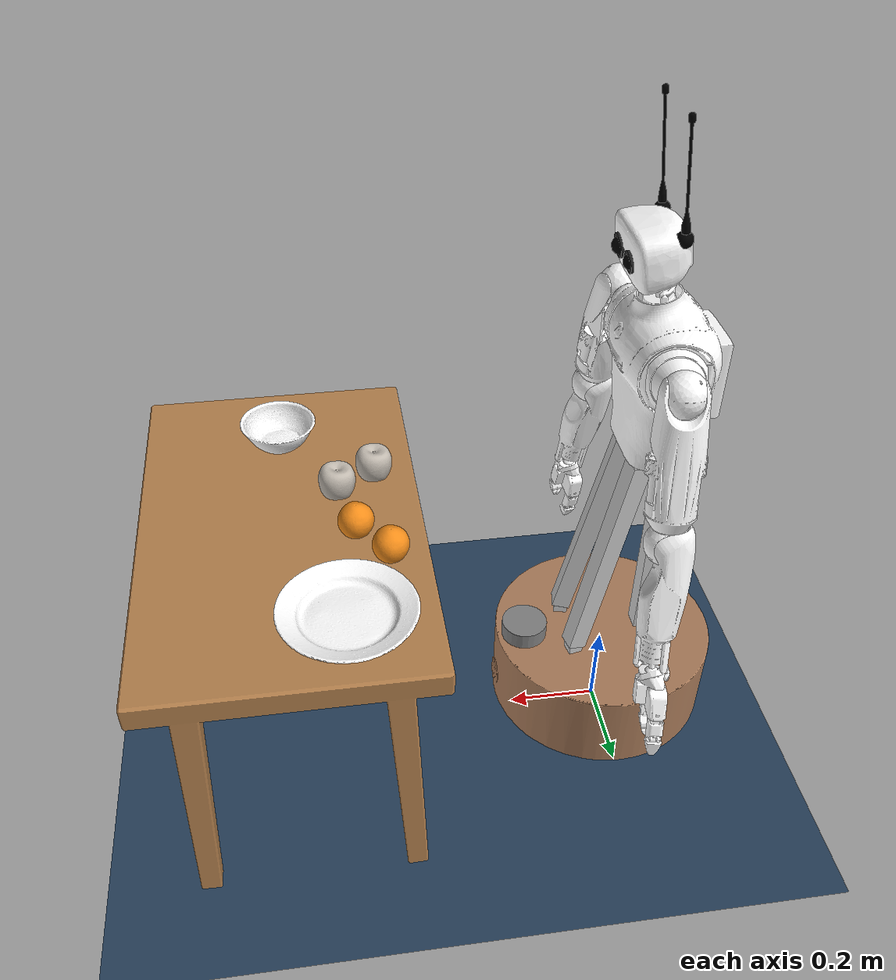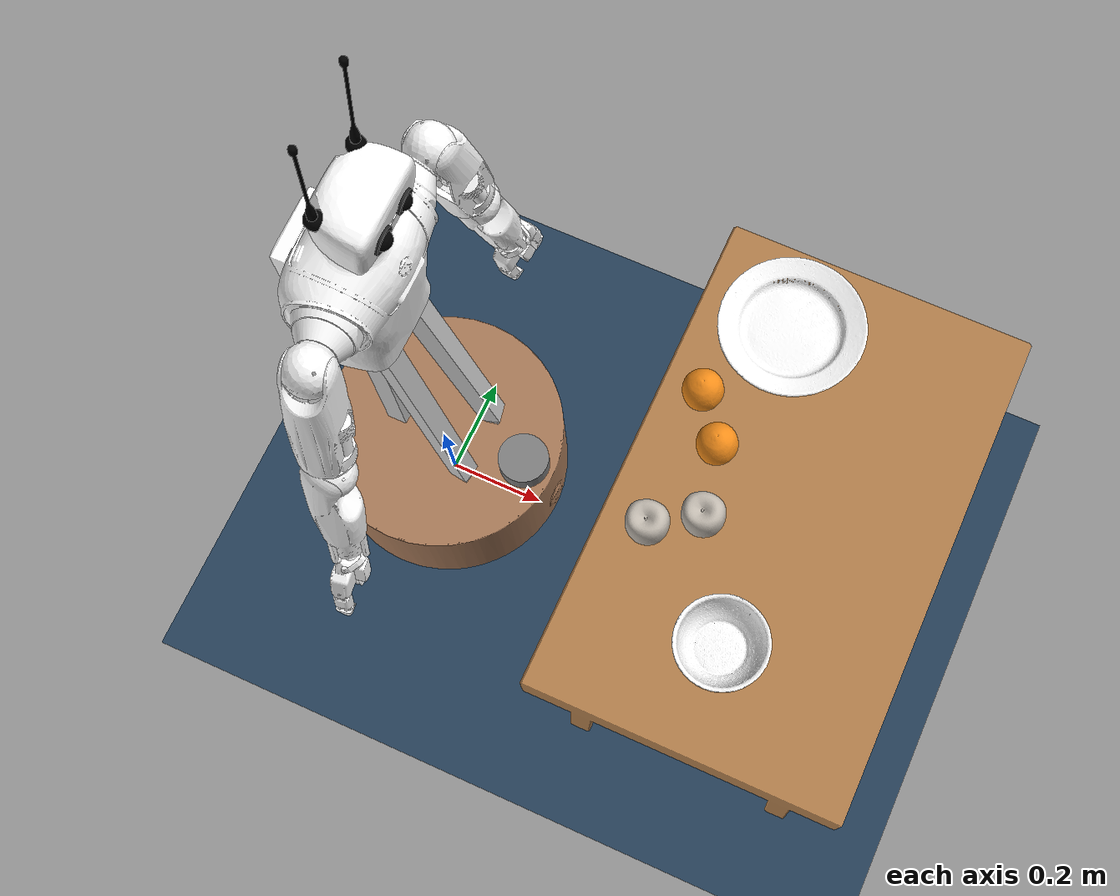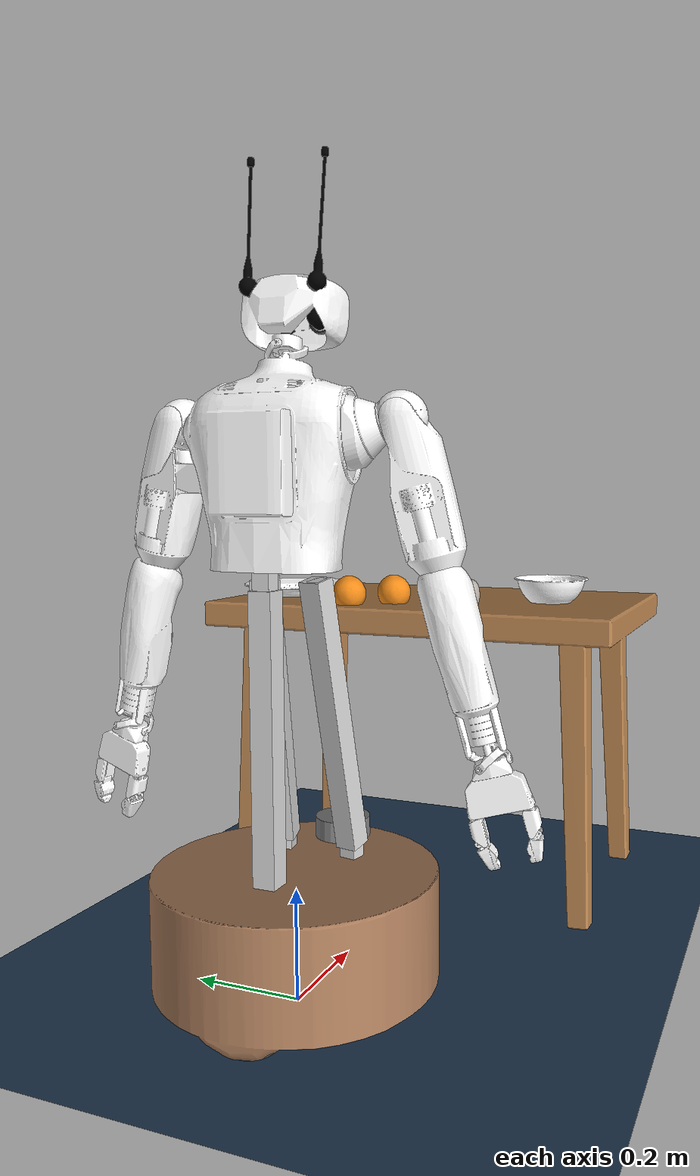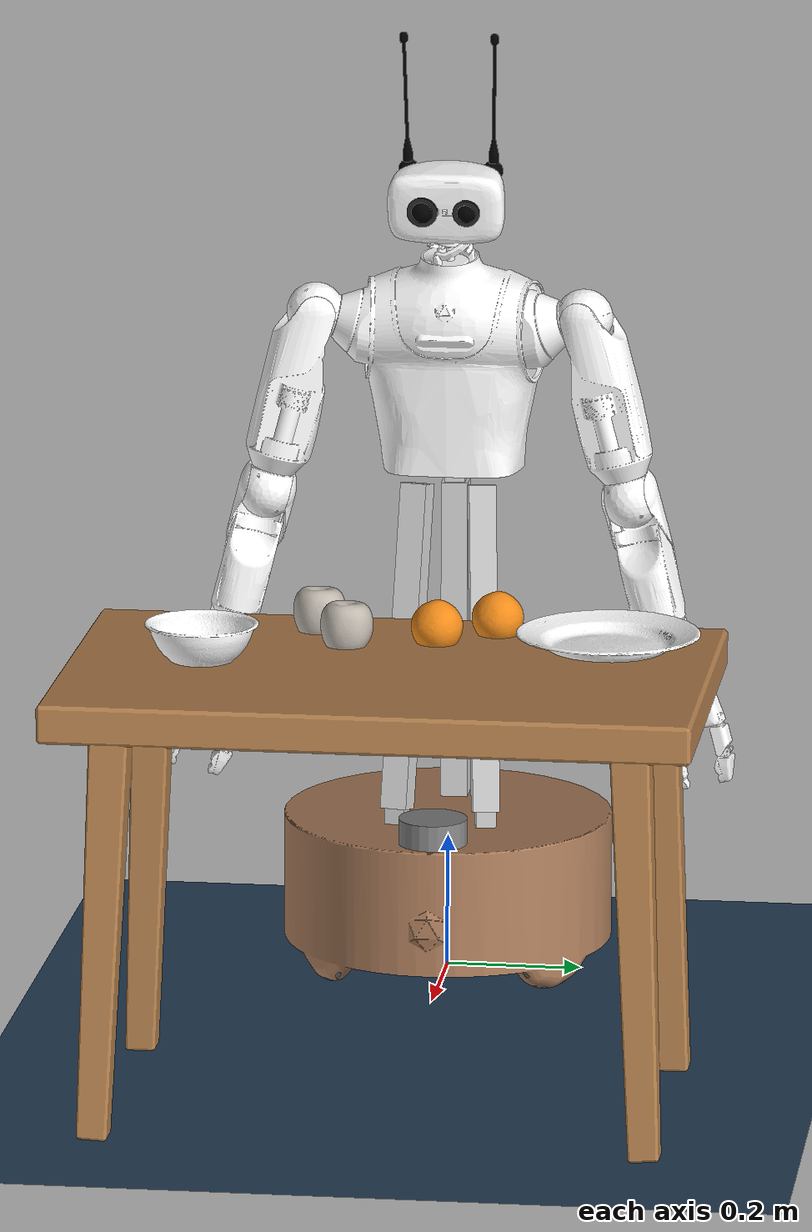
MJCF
<mujoco model="reachy2fruits_scene">
    <compiler angle="radian" />

    <include file="../assets/reachy2_asset.xml"/>
    <include file="../assets/fruits_assets.xml"/>
    <include file="../assets/bowl_asset.xml"/>
    <include file="../assets/plate_asset.xml"/>
    <include file="../assets/table_asset.xml"/>

    <custom>
        <text name="tracked_bodies" data="torso, apple1, apple2, orange1, orange2" />
    </custom>

    <default>
        <default class="ycb_col">
            <geom contype="1" rgba = "1 1 1 1" conaffinity="1" condim ="6" solimp="0.95 0.99 0.001" solref=".002 1" margin = "0.002" friction="0.5 0.1 0.01" group = "3"/>
        </default>
        <default class="ycb_viz">
            <geom contype="0" conaffinity="0" type="mesh"/>
        </default>

    </default>

    <option gravity="0 0 -9.81" timestep="0.001" iterations="50" integrator="implicitfast">
        <flag multiccd="enable" contact="enable"/>
    </option>

    <visual>
        <headlight diffuse="0.6 0.6 0.6" ambient="0.3 0.3 0.3" specular="0 0 0"/>
        <rgba haze="0.15 0.25 0.35 1"/>
        <global azimuth="160" elevation="-20" offwidth="1280" offheight="720"/>
    </visual>

    <asset>
        <!-- Ground -->
        <texture type="skybox" builtin="gradient" rgb1="0.3 0.5 0.7" rgb2="0 0 0" width="512" height="3072"/>
        <texture type="2d" name="groundplane" builtin="checker" rgb1="0.2 0.3 0.4" rgb2="0.1 0.2 0.3" markrgb="0.8 0.8 0.8" width="300" height="300"/>
        <material name="groundplane" texture="groundplane" texuniform="true" texrepeat="5 5" reflectance="0.2"/>
    </asset>

    <worldbody>
        <light pos="0 0 3" dir="0 0 -1" directional="false"/>

        <!-- Sol -->
        <body name="floor">
            <geom contype="1" conaffinity="2" friction=".1 0.005 0.0001" name="floor" pos="0 0 0" size="0 0 .25" type="plane" material="groundplane" condim="3" solimp="0 0.95 0.001 0.5 2" solref="0.02 1" margin="0"/>
        </body>

        <!-- Reachy -->
        <body name="reachy" pos="0 0 0">
            <freejoint name="mobile_base" />
            <include file="../objects/reachy2_body.xml"/>
        </body>

        <!-- Table -->
        <body name="table" pos="0.7 0 0" euler="1.57 1.57 0">
            <geom class = "ycb_viz" name="table_visual"  mesh="wooden_table" material="wooden_table_material"/>
            <geom class = "ycb_col" name="table_collision" type="box" size="0.45 0.34 0.28" pos="0 0.3 0" margin = "0" friction="1 0.005 0.0005" solref="0.03 1" solimp="0.99 0.99 0.01"/>

        </body>

        <!-- Apples -->
        <body name="apple1" pos="0.5 -0.12 0.63" >
            <geom class="ycb_viz" material="apple_mat" mesh="apple"/>
            <geom class = "ycb_col" type="capsule" fromto="0.0 -0.005 0.035 0.0 -0.005 0.055" size="0.035" mass="0.1" rgba = "1 0 0 1"/>
            <joint type="free"/>
        </body>

        <body name="apple2" pos="0.58 -0.07 0.63" >
            <geom class="ycb_viz" material="apple_mat" mesh="apple"/>
            <geom class = "ycb_col" type="capsule" fromto="0.0 -0.005 0.035 0.0 -0.005 0.055" size="0.035" mass="0.1" rgba = "1 0 0 1"/>
            <joint type="free"/>
        </body>

        <!-- Oranges -->
        <body name="orange1" pos="0.5 0.15 0.63">
            <geom class="ycb_viz" material="orange_mat" mesh="orange"/>
            <geom class = "ycb_col" type="capsule" fromto="-0.007 -0.018 0.035 -0.007 -0.018 0.055" size="0.038" mass="0.1" rgba = "1 0 0 1"/>
            <joint type="free"/>
        </body>

        <body name="orange2" pos="0.56 0.07 0.63">
            <geom class="ycb_viz" material="orange_mat" mesh="orange"/>
            <geom class = "ycb_col" type="capsule" fromto="-0.007 -0.018 0.035 -0.007 -0.018 0.055" size="0.038" mass="0.1" rgba = "1 0 0 1"/>
            <joint type="free"/>
        </body>

        <!-- White Plate -->
        <body pos="0.6 0.3 0.65" euler="0 0 0">
			<include file="../objects/plate_body.xml" />
            <freejoint name="plate"/>
		</body>

        <!-- Bowl -->
        <body pos="0.65 -0.25 0.64" euler="0 0 1.57">
			<include file="../objects/bowl_body.xml" />
            <freejoint name="bowl"/>
		</body>
    </worldbody>

</mujoco>

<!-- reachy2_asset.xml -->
<mujocoinclude>

    <asset>
        <mesh name="mobile_base_visual" file="../assets/meshes/reachy2/mobile_base_visual.obj" />
        <mesh name="torso_visual" file="../assets/meshes/reachy2/torso_visual.obj" />
        <mesh name="torso_collider" file="../assets/meshes/reachy2/torso_collider.obj" />
        <mesh name="head_visual" file="../assets/meshes/reachy2/head_visual.obj" />
        <mesh name="head_collider" file="../assets/meshes/reachy2/head_collider.obj" />
        <mesh name="head_antenna_visual" file="../assets/meshes/reachy2/head_antenna_visual.obj" />
        <mesh name="2D_sphere_visual" file="../assets/meshes/reachy2/2D_sphere_visual.obj" />
        <mesh name="upper_arm_visual" file="../assets/meshes/reachy2/upper_arm_visual.obj" />
        <mesh name="upper_arm_collider" file="../assets/meshes/reachy2/upper_arm_collider.obj" />
        <mesh name="forearm_visual" file="../assets/meshes/reachy2/forearm_visual.obj" />
        <mesh name="forearm_collider" file="../assets/meshes/reachy2/forearm_collider.obj" />
        <mesh name="pincette_base_collider" file="../assets/meshes/reachy2/pincette_base_collider.obj" />
        <mesh name="pincette_base_visual" file="../assets/meshes/reachy2/pincette_base_visual.obj" />
        <mesh name="pincette_proximal_collider" file="../assets/meshes/reachy2/pincette_proximal_collider.obj" />
        <mesh name="pincette_proximal_visual" file="../assets/meshes/reachy2/pincette_proximal_visual.obj" />
        <mesh name="pincette_distal_collider" file="../assets/meshes/reachy2/pincette_distal_collider.obj" />
        <mesh name="pincette_distal" file="../assets/meshes/reachy2/pincette_distal.obj" />
        <texture builtin="checker" height="10" name="texplane" rgb1="0 0 0" rgb2="0.8 0.8 0.8" type="2d" width="10" />
        <material name="checkmat" reflectance="0.5" shininess="1" specular="1" texrepeat="6 6" texture="texplane" />

    </asset>

    <default>
        <joint damping="10" frictionloss="2.0" actuatorfrcrange="-2000 2000" armature="1.0"/>
        <position kp="500" kv="10" />

        <default class="gripper">
        <joint damping="5.0" frictionloss="0.5" actuatorfrcrange="-40 40" armature="1.0"/>
        <position kp="150" kv="5" />
        </default>

        <default class="tripod">
        <joint damping="1000" frictionloss="50.0" actuatorfrcrange="-20000 20000" armature="5.0"/>
        <position kp="50000" kv="5000" />
        </default>

        <default class="wheel">
        <joint  armature="0.1" />
        </default>

        <default class="visual">
        <geom type="mesh" mass="0" group="2" contype="0" conaffinity="0"/>
        </default>

        <default class="collider">
        <geom group="3" type="mesh" condim="6" friction="1 5e-3 5e-4" solref=".01 1" contype="1"
            conaffinity="1" />
        </default>

        <default class="gripper_collider">
        <geom group="3" type="mesh" condim="6" friction="1.0 0.5 0.01" solref=".01 1" contype="1"
            conaffinity="1" />
        </default>

        <default class="gripper_collider_box">
        <geom group="3" type="box" friction="4.0 1.0 0.01" condim="6" contype="1" conaffinity="1"
            solimp="0.95 0.99 0.01" solref="0.002 1" margin="0.001"/>

        </default>

        <default class="wheel_collision">
        <geom friction="0.3 0.005 0.0001" condim="3" contype="2" conaffinity="0"
            solimp="0 0.95 0.001 0.5 2" solref="0.02 1" margin="0" />
        </default>

    </default>

    <equality>
        <joint
        joint1="r_hand_finger"
        joint2="r_hand_finger_proximal"
        polycoef="0.554 -0.4689 0 0 0"
        solimp="0.95 0.99 0.001"
        solref="0.005 1"
        />
        <joint
        joint1="r_hand_finger_proximal"
        joint2="r_hand_finger_distal"
        polycoef="0 -1 0 0 0"
        solimp="0.95 0.99 0.001"
        solref="0.005 1"
        />
        <joint
        joint1="r_hand_finger_proximal"
        joint2="r_hand_finger_proximal_mimic"
        polycoef="0 1 0 0 0"
        solimp="0.95 0.99 0.001"
        solref="0.005 1"
        />
        <joint
        joint1="r_hand_finger_distal"
        joint2="r_hand_finger_distal_mimic"
        polycoef="0 1 0 0 0"
        solimp="0.95 0.99 0.001"
        solref="0.005 1"
        />
        <joint
        joint1="l_hand_finger"
        joint2="l_hand_finger_proximal"
        polycoef="0.554 -0.4689 0 0 0"
        solimp="0.95 0.99 0.001"
        solref="0.005 1"
        />
        <joint
        joint1="l_hand_finger_proximal"
        joint2="l_hand_finger_distal"
        polycoef="0 -1 0 0 0"
        solimp="0.95 0.99 0.001"
        solref="0.005 1"
        />
        <joint
        joint1="l_hand_finger_proximal"
        joint2="l_hand_finger_proximal_mimic"
        polycoef="0 1 0 0 0"
        solimp="0.95 0.99 0.001"
        solref="0.005 1"
        />
        <joint
        joint1="l_hand_finger_distal"
        joint2="l_hand_finger_distal_mimic"
        polycoef="0 1 0 0 0"
        solimp="0.95 0.99 0.001"
        solref="0.005 1"
        />

        <joint
        joint1="left_bar_joint_mimic"
        joint2="tripod_joint"
        polycoef="0 0.40967047 -0.74428024 0.82037152 0"
        solimp="0.95 0.99 0.001"
        solref="0.005 1"
        />

        <joint
        joint1="tripod_joint"
        joint2="left_bar_prism_joint_mimic"
        polycoef="0 -0.9861535348976198 0 0 0"
        solimp="0.95 0.99 0.001"
        solref="0.005 1"
        />

        <joint
        joint1="right_bar_joint_mimic"
        joint2="tripod_joint"
        polycoef="0 0.40967047 -0.74428024 0.82037152 0"
        solimp="0.95 0.99 0.001"
        solref="0.005 1"
        />
        <joint
        joint1="tripod_joint"
        joint2="right_bar_prism_joint_mimic"
        polycoef="0 -0.9861535348976198 0 0 0"
        solimp="0.95 0.99 0.001"
        solref="0.005 1"
        />

    </equality>
    <actuator>
        <position name="tripod_joint" joint="tripod_joint" gear="1" inheritrange="1" class="tripod" />

        <position name="neck_roll" joint="neck_roll" gear="1" inheritrange="1" />
        <position name="neck_pitch" joint="neck_pitch" gear="1" inheritrange="1" />
        <position name="neck_yaw" joint="neck_yaw" gear="1" inheritrange="1" />

        <position name="antenna_left" joint="antenna_left" gear="1" inheritrange="1" />
        <position name="antenna_right" joint="antenna_right" gear="1" inheritrange="1" />

        <position
        name="l_shoulder_pitch"
        joint="l_shoulder_pitch"
        gear="1"
        inheritrange="1"
        />
        <position
        name="l_shoulder_roll"
        joint="l_shoulder_roll"
        gear="1"
        inheritrange="1"
        />
        <position
        name="l_elbow_yaw"
        joint="l_elbow_yaw"
        gear="1"
        inheritrange="1"
        />
        <position
        name="l_elbow_pitch"
        joint="l_elbow_pitch"
        gear="1"
        inheritrange="1"
        />
        <position
        name="l_wrist_roll"
        joint="l_wrist_roll"
        gear="1"
        inheritrange="1"
        />
        <position
        name="l_wrist_pitch"
        joint="l_wrist_pitch"
        gear="1"
        inheritrange="1"
        />
        <position
        name="l_wrist_yaw"
        joint="l_wrist_yaw"
        gear="1"
        inheritrange="1"
        />
        <position
        name="r_shoulder_pitch"
        joint="r_shoulder_pitch"
        gear="1"
        inheritrange="1"
        />
        <position
        name="r_shoulder_roll"
        joint="r_shoulder_roll"
        gear="1"
        inheritrange="1"
        />
        <position
        name="r_elbow_yaw"
        joint="r_elbow_yaw"
        gear="1"
        inheritrange="1"
        />
        <position
        name="r_elbow_pitch"
        joint="r_elbow_pitch"
        gear="1"
        inheritrange="1"
        />
        <position
        name="r_wrist_roll"
        joint="r_wrist_roll"
        gear="1"
        inheritrange="1"
        />
        <position
        name="r_wrist_pitch"
        joint="r_wrist_pitch"
        gear="1"
        inheritrange="1"
        />
        <position
        name="r_wrist_yaw"
        joint="r_wrist_yaw"
        gear="1"
        inheritrange="1"
        />
        <position
        name="r_hand_finger"
        joint="r_hand_finger"
        gear="1"
        inheritrange="1"
        class="gripper"
        />
        <position
        name="l_hand_finger"
        joint="l_hand_finger"
        gear="1"
        inheritrange="1"
        class="gripper"
        />

        <motor
        name="drivewhl2_joint"
        joint="drivewhl2_joint"
        ctrlrange="-50 50" ctrllimited="true"
        />
        <motor
        name="drivewhl1_joint"
        joint="drivewhl1_joint"
        ctrlrange="-50 50" ctrllimited="true"
        />
        <motor
        name="drivewhl3_joint"
        joint="drivewhl3_joint"
        ctrlrange="-50 50" ctrllimited="true"
        />

    </actuator>

    <contact>
        <exclude name="torso_r_shoulder" body1="torso" body2="r_elbow_arm_link" />
        <exclude name="torso_l_shoulder" body1="torso" body2="l_elbow_arm_link" />

        <exclude name="l_arm_forearm" body1="l_elbow_arm_link" body2="l_elbow_forearm_link" />
        <exclude name="r_arm_forearm" body1="r_elbow_arm_link" body2="r_elbow_forearm_link" />

        <exclude name="l_forearm_gripper" body1="l_elbow_forearm_link" body2="l_hand_palm_link" />
        <exclude name="r_forearm_gripper" body1="r_elbow_forearm_link" body2="r_hand_palm_link" />

        <exclude name="back_bar" body1="back_bar_base" body2="back_bar_inner" />
    </contact>

</mujocoinclude>

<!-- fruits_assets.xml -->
<mujocoinclude>
    <asset>
        <texture type="2d" name="apple_tex" file="../assets/textures/apple_texture.png"/>
        <material name="apple_mat" texture="apple_tex" specular="0.5" shininess="0.5"/>
        <mesh file="../assets/meshes/apple/apple.obj" name="apple"/>
        <mesh file="../assets/meshes/apple/apple_collision.obj" name="apple_collision" />

        <texture type="2d" name="orange_texture" file="../assets/textures/orange_texture.png"/>
        <material name="orange_mat" texture="orange_texture" specular="0.5" shininess="0.5"/>
        <mesh file="../assets/meshes/orange/textured.obj" name="orange"/>
        <mesh file="../assets/meshes/orange/textured_collision_0.obj" name="orange_collision_0"/>

    </asset>
</mujocoinclude>

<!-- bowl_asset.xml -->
<mujocoinclude>
    <asset>
        <material name="bowl_mat" rgba="1 1 1 1" specular="0.5" shininess="0.5"/>
        <mesh file="../assets/meshes/bowl/textured.obj" name="bowl"/>
        <mesh file="../assets/meshes/bowl/textured_collision_0.obj" name="bowl_collision_0"/>
        <mesh file="../assets/meshes/bowl/textured_collision_1.obj" name="bowl_collision_1"/>
        <mesh file="../assets/meshes/bowl/textured_collision_2.obj" name="bowl_collision_2"/>
        <mesh file="../assets/meshes/bowl/textured_collision_3.obj" name="bowl_collision_3"/>
        <mesh file="../assets/meshes/bowl/textured_collision_4.obj" name="bowl_collision_4"/>
        <mesh file="../assets/meshes/bowl/textured_collision_5.obj" name="bowl_collision_5"/>
        <mesh file="../assets/meshes/bowl/textured_collision_6.obj" name="bowl_collision_6"/>
        <mesh file="../assets/meshes/bowl/textured_collision_7.obj" name="bowl_collision_7"/>
        <mesh file="../assets/meshes/bowl/textured_collision_8.obj" name="bowl_collision_8"/>
        <mesh file="../assets/meshes/bowl/textured_collision_9.obj" name="bowl_collision_9"/>
        <mesh file="../assets/meshes/bowl/textured_collision_10.obj" name="bowl_collision_10"/>
        <mesh file="../assets/meshes/bowl/textured_collision_11.obj" name="bowl_collision_11"/>
        <mesh file="../assets/meshes/bowl/textured_collision_12.obj" name="bowl_collision_12"/>
        <mesh file="../assets/meshes/bowl/textured_collision_13.obj" name="bowl_collision_13"/>
        <mesh file="../assets/meshes/bowl/textured_collision_14.obj" name="bowl_collision_14"/>
        <mesh file="../assets/meshes/bowl/textured_collision_15.obj" name="bowl_collision_15"/>
        <mesh file="../assets/meshes/bowl/textured_collision_16.obj" name="bowl_collision_16"/>
        <mesh file="../assets/meshes/bowl/textured_collision_17.obj" name="bowl_collision_17"/>
        <mesh file="../assets/meshes/bowl/textured_collision_18.obj" name="bowl_collision_18"/>
        <mesh file="../assets/meshes/bowl/textured_collision_19.obj" name="bowl_collision_19"/>
        <mesh file="../assets/meshes/bowl/textured_collision_20.obj" name="bowl_collision_20"/>
        <mesh file="../assets/meshes/bowl/textured_collision_21.obj" name="bowl_collision_21"/>
        <mesh file="../assets/meshes/bowl/textured_collision_22.obj" name="bowl_collision_22"/>
        <mesh file="../assets/meshes/bowl/textured_collision_23.obj" name="bowl_collision_23"/>
        <mesh file="../assets/meshes/bowl/textured_collision_24.obj" name="bowl_collision_24"/>
        <mesh file="../assets/meshes/bowl/textured_collision_25.obj" name="bowl_collision_25"/>
        <mesh file="../assets/meshes/bowl/textured_collision_26.obj" name="bowl_collision_26"/>
        <mesh file="../assets/meshes/bowl/textured_collision_27.obj" name="bowl_collision_27"/>
        <mesh file="../assets/meshes/bowl/textured_collision_28.obj" name="bowl_collision_28"/>
        <mesh file="../assets/meshes/bowl/textured_collision_29.obj" name="bowl_collision_29"/>
        <mesh file="../assets/meshes/bowl/textured_collision_30.obj" name="bowl_collision_30"/>
        <mesh file="../assets/meshes/bowl/textured_collision_31.obj" name="bowl_collision_31"/>
        <mesh file="../assets/meshes/bowl/textured_collision_32.obj" name="bowl_collision_32"/>
        <mesh file="../assets/meshes/bowl/textured_collision_33.obj" name="bowl_collision_33"/>
        <mesh file="../assets/meshes/bowl/textured_collision_34.obj" name="bowl_collision_34"/>
        <mesh file="../assets/meshes/bowl/textured_collision_35.obj" name="bowl_collision_35"/>
        <mesh file="../assets/meshes/bowl/textured_collision_36.obj" name="bowl_collision_36"/>
        <mesh file="../assets/meshes/bowl/textured_collision_37.obj" name="bowl_collision_37"/>
        <mesh file="../assets/meshes/bowl/textured_collision_38.obj" name="bowl_collision_38"/>
        <mesh file="../assets/meshes/bowl/textured_collision_39.obj" name="bowl_collision_39"/>
        <mesh file="../assets/meshes/bowl/textured_collision_40.obj" name="bowl_collision_40"/>
        <mesh file="../assets/meshes/bowl/textured_collision_41.obj" name="bowl_collision_41"/>
        <mesh file="../assets/meshes/bowl/textured_collision_42.obj" name="bowl_collision_42"/>
        <mesh file="../assets/meshes/bowl/textured_collision_43.obj" name="bowl_collision_43"/>
        <mesh file="../assets/meshes/bowl/textured_collision_44.obj" name="bowl_collision_44"/>
        <mesh file="../assets/meshes/bowl/textured_collision_45.obj" name="bowl_collision_45"/>
        <mesh file="../assets/meshes/bowl/textured_collision_46.obj" name="bowl_collision_46"/>
        <mesh file="../assets/meshes/bowl/textured_collision_47.obj" name="bowl_collision_47"/>
        <mesh file="../assets/meshes/bowl/textured_collision_48.obj" name="bowl_collision_48"/>
        <mesh file="../assets/meshes/bowl/textured_collision_49.obj" name="bowl_collision_49"/>
        <mesh file="../assets/meshes/bowl/textured_collision_50.obj" name="bowl_collision_50"/>
        <mesh file="../assets/meshes/bowl/textured_collision_51.obj" name="bowl_collision_51"/>
        <mesh file="../assets/meshes/bowl/textured_collision_52.obj" name="bowl_collision_52"/>
        <mesh file="../assets/meshes/bowl/textured_collision_53.obj" name="bowl_collision_53"/>
        <mesh file="../assets/meshes/bowl/textured_collision_54.obj" name="bowl_collision_54"/>
        <mesh file="../assets/meshes/bowl/textured_collision_55.obj" name="bowl_collision_55"/>
        <mesh file="../assets/meshes/bowl/textured_collision_56.obj" name="bowl_collision_56"/>
        <mesh file="../assets/meshes/bowl/textured_collision_57.obj" name="bowl_collision_57"/>
        <mesh file="../assets/meshes/bowl/textured_collision_58.obj" name="bowl_collision_58"/>
        <mesh file="../assets/meshes/bowl/textured_collision_59.obj" name="bowl_collision_59"/>
        <mesh file="../assets/meshes/bowl/textured_collision_60.obj" name="bowl_collision_60"/>
        <mesh file="../assets/meshes/bowl/textured_collision_61.obj" name="bowl_collision_61"/>
        <mesh file="../assets/meshes/bowl/textured_collision_62.obj" name="bowl_collision_62"/>
        <mesh file="../assets/meshes/bowl/textured_collision_63.obj" name="bowl_collision_63"/>
        <mesh file="../assets/meshes/bowl/textured_collision_64.obj" name="bowl_collision_64"/>
        <mesh file="../assets/meshes/bowl/textured_collision_65.obj" name="bowl_collision_65"/>
        <mesh file="../assets/meshes/bowl/textured_collision_66.obj" name="bowl_collision_66"/>
        <mesh file="../assets/meshes/bowl/textured_collision_67.obj" name="bowl_collision_67"/>
        <mesh file="../assets/meshes/bowl/textured_collision_68.obj" name="bowl_collision_68"/>
        <mesh file="../assets/meshes/bowl/textured_collision_69.obj" name="bowl_collision_69"/>
        <mesh file="../assets/meshes/bowl/textured_collision_70.obj" name="bowl_collision_70"/>
        <mesh file="../assets/meshes/bowl/textured_collision_71.obj" name="bowl_collision_71"/>
        <mesh file="../assets/meshes/bowl/textured_collision_72.obj" name="bowl_collision_72"/>
        <mesh file="../assets/meshes/bowl/textured_collision_73.obj" name="bowl_collision_73"/>
        <mesh file="../assets/meshes/bowl/textured_collision_74.obj" name="bowl_collision_74"/>
        <mesh file="../assets/meshes/bowl/textured_collision_75.obj" name="bowl_collision_75"/>
        <mesh file="../assets/meshes/bowl/textured_collision_76.obj" name="bowl_collision_76"/>
        <mesh file="../assets/meshes/bowl/textured_collision_77.obj" name="bowl_collision_77"/>
        <mesh file="../assets/meshes/bowl/textured_collision_78.obj" name="bowl_collision_78"/>
        <mesh file="../assets/meshes/bowl/textured_collision_79.obj" name="bowl_collision_79"/>
    </asset>
</mujocoinclude>

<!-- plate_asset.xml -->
<mujocoinclude>
    <asset>
        <material name="plate_mat" rgba="1 1 1 1" specular="0.5" shininess="0.5"/>
        <mesh file="../assets/meshes/plate/textured.obj" name="plate"/>
        <mesh file="../assets/meshes/plate/textured_collision_0.obj" name="plate_collision_0"/>
        <mesh file="../assets/meshes/plate/textured_collision_1.obj" name="plate_collision_1"/>
        <mesh file="../assets/meshes/plate/textured_collision_2.obj" name="plate_collision_2"/>
        <mesh file="../assets/meshes/plate/textured_collision_3.obj" name="plate_collision_3"/>
        <mesh file="../assets/meshes/plate/textured_collision_4.obj" name="plate_collision_4"/>
        <mesh file="../assets/meshes/plate/textured_collision_5.obj" name="plate_collision_5"/>
        <mesh file="../assets/meshes/plate/textured_collision_6.obj" name="plate_collision_6"/>
        <mesh file="../assets/meshes/plate/textured_collision_7.obj" name="plate_collision_7"/>
        <mesh file="../assets/meshes/plate/textured_collision_8.obj" name="plate_collision_8"/>
        <mesh file="../assets/meshes/plate/textured_collision_9.obj" name="plate_collision_9"/>
        <mesh file="../assets/meshes/plate/textured_collision_10.obj" name="plate_collision_10"/>
        <mesh file="../assets/meshes/plate/textured_collision_11.obj" name="plate_collision_11"/>
        <mesh file="../assets/meshes/plate/textured_collision_12.obj" name="plate_collision_12"/>
        <mesh file="../assets/meshes/plate/textured_collision_13.obj" name="plate_collision_13"/>
        <mesh file="../assets/meshes/plate/textured_collision_14.obj" name="plate_collision_14"/>
        <mesh file="../assets/meshes/plate/textured_collision_15.obj" name="plate_collision_15"/>
        <mesh file="../assets/meshes/plate/textured_collision_16.obj" name="plate_collision_16"/>
        <mesh file="../assets/meshes/plate/textured_collision_17.obj" name="plate_collision_17"/>
        <mesh file="../assets/meshes/plate/textured_collision_18.obj" name="plate_collision_18"/>
        <mesh file="../assets/meshes/plate/textured_collision_19.obj" name="plate_collision_19"/>
        <mesh file="../assets/meshes/plate/textured_collision_20.obj" name="plate_collision_20"/>
        <mesh file="../assets/meshes/plate/textured_collision_21.obj" name="plate_collision_21"/>
        <mesh file="../assets/meshes/plate/textured_collision_22.obj" name="plate_collision_22"/>
        <mesh file="../assets/meshes/plate/textured_collision_23.obj" name="plate_collision_23"/>
        <mesh file="../assets/meshes/plate/textured_collision_24.obj" name="plate_collision_24"/>
        <mesh file="../assets/meshes/plate/textured_collision_25.obj" name="plate_collision_25"/>
        <mesh file="../assets/meshes/plate/textured_collision_26.obj" name="plate_collision_26"/>
        <mesh file="../assets/meshes/plate/textured_collision_27.obj" name="plate_collision_27"/>
        <mesh file="../assets/meshes/plate/textured_collision_28.obj" name="plate_collision_28"/>
        <mesh file="../assets/meshes/plate/textured_collision_29.obj" name="plate_collision_29"/>
        <mesh file="../assets/meshes/plate/textured_collision_30.obj" name="plate_collision_30"/>
        <mesh file="../assets/meshes/plate/textured_collision_31.obj" name="plate_collision_31"/>
        <mesh file="../assets/meshes/plate/textured_collision_32.obj" name="plate_collision_32"/>
        <mesh file="../assets/meshes/plate/textured_collision_33.obj" name="plate_collision_33"/>
        <mesh file="../assets/meshes/plate/textured_collision_34.obj" name="plate_collision_34"/>
        <mesh file="../assets/meshes/plate/textured_collision_35.obj" name="plate_collision_35"/>
        <mesh file="../assets/meshes/plate/textured_collision_36.obj" name="plate_collision_36"/>
        <mesh file="../assets/meshes/plate/textured_collision_37.obj" name="plate_collision_37"/>
        <mesh file="../assets/meshes/plate/textured_collision_38.obj" name="plate_collision_38"/>
        <mesh file="../assets/meshes/plate/textured_collision_39.obj" name="plate_collision_39"/>
        <mesh file="../assets/meshes/plate/textured_collision_40.obj" name="plate_collision_40"/>
        <mesh file="../assets/meshes/plate/textured_collision_41.obj" name="plate_collision_41"/>
        <mesh file="../assets/meshes/plate/textured_collision_42.obj" name="plate_collision_42"/>
        <mesh file="../assets/meshes/plate/textured_collision_43.obj" name="plate_collision_43"/>
        <mesh file="../assets/meshes/plate/textured_collision_44.obj" name="plate_collision_44"/>
        <mesh file="../assets/meshes/plate/textured_collision_45.obj" name="plate_collision_45"/>
        <mesh file="../assets/meshes/plate/textured_collision_46.obj" name="plate_collision_46"/>
        <mesh file="../assets/meshes/plate/textured_collision_47.obj" name="plate_collision_47"/>
        <mesh file="../assets/meshes/plate/textured_collision_48.obj" name="plate_collision_48"/>
        <mesh file="../assets/meshes/plate/textured_collision_49.obj" name="plate_collision_49"/>
        <mesh file="../assets/meshes/plate/textured_collision_50.obj" name="plate_collision_50"/>
        <mesh file="../assets/meshes/plate/textured_collision_51.obj" name="plate_collision_51"/>
        <mesh file="../assets/meshes/plate/textured_collision_52.obj" name="plate_collision_52"/>
        <mesh file="../assets/meshes/plate/textured_collision_53.obj" name="plate_collision_53"/>
        <mesh file="../assets/meshes/plate/textured_collision_54.obj" name="plate_collision_54"/>
        <mesh file="../assets/meshes/plate/textured_collision_55.obj" name="plate_collision_55"/>
        <mesh file="../assets/meshes/plate/textured_collision_56.obj" name="plate_collision_56"/>
        <mesh file="../assets/meshes/plate/textured_collision_57.obj" name="plate_collision_57"/>
        <mesh file="../assets/meshes/plate/textured_collision_58.obj" name="plate_collision_58"/>
        <mesh file="../assets/meshes/plate/textured_collision_59.obj" name="plate_collision_59"/>
        <mesh file="../assets/meshes/plate/textured_collision_60.obj" name="plate_collision_60"/>
        <mesh file="../assets/meshes/plate/textured_collision_61.obj" name="plate_collision_61"/>
        <mesh file="../assets/meshes/plate/textured_collision_62.obj" name="plate_collision_62"/>
        <mesh file="../assets/meshes/plate/textured_collision_63.obj" name="plate_collision_63"/>
        <mesh file="../assets/meshes/plate/textured_collision_64.obj" name="plate_collision_64"/>

    </asset>
</mujocoinclude>

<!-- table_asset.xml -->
<mujocoinclude>
    <asset>
        <texture type="2d" name="wooden_table_texture" file="../assets/textures/wood0.png"/>
        <material name="wooden_table_material" texture="wooden_table_texture"/>
        <mesh name="wooden_table" file="../assets/meshes/wooden_table.obj" scale="0.8 0.8 0.8"/>
    </asset>
</mujocoinclude>

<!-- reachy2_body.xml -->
<mujocoinclude>
    <body name="base_link">
        <inertial pos="0.008 -0.00048 0.112" quat="-0.0363977 0.704069 0.0372966 0.708217" mass="24"
            diaginertia="0.709918 0.423857 0.407726" />
        <geom type="mesh" mesh="mobile_base_visual" class="visual" friction="5 0.1 0.01" rgba="0.66  0.48 0.35 1"/>
        <geom size="0.245 0.095" pos="0 0 0.145" type="cylinder" class="collider" />
        <body name="drivewhl1_link" pos="0.099 -0.171473 0.105" quat="0.965926 0 0 0.258819">
            <inertial pos="0 0 0" quat="0.5 0.5 -0.5 0.5" mass="0.5"
            diaginertia="0.00275625 0.00142917 0.00142917"/>
            <joint name="drivewhl1_joint" pos="0 0 0" axis="0 1 0" class="wheel" />

            <geom size="0.105 0.105 0.0175" quat="0.707107 0.707107 0 0" type="ellipsoid" class="visual" />
            <body pos="0.0 0.0 0.0945" euler="0 0 0">
            <inertial pos="0 0 0.0" quat="1 0 0 0" mass="0.01" diaginertia="0.0001 0.0001 0.0001" />
            <geom size="0.0105 0.0105 0.04" quat="0.707107 0 0.707107  0" type="ellipsoid"
                material="checkmat" class="visual" />
            <geom size="0.0105 0.0105 0.04" quat="0.707107 0 0.707107  0" type="ellipsoid"
                class="wheel_collision" />
            <joint pos="0 0 0" axis="1 0 0" />
            </body>

            <body pos="0.0 0.0 -0.0945" euler="0 0 0">
            <inertial pos="0 0 0.0" quat="1 0 0 0" mass="0.01" diaginertia="0.0001 0.0001 0.0001" />
            <geom size="0.0105 0.0105 0.04" quat="0.707107 0 0.707107  0" type="ellipsoid"
                material="checkmat" class="visual" />
            <geom size="0.0105 0.0105 0.04" quat="0.707107 0 0.707107  0" type="ellipsoid"
                class="wheel_collision" />
            <joint pos="0 0 0" axis="1 0 0" />
            </body>

            <body pos="0.0945 0.0 0.0" euler="0 1.5707963267948966 0">
            <inertial pos="0 0 0.0" quat="1 0 0 0" mass="0.01" diaginertia="0.0001 0.0001 0.0001" />
            <geom size="0.0105 0.0105 0.04" quat="0.707107 0 0.707107  0" type="ellipsoid"
                material="checkmat" class="visual" />
            <geom size="0.0105 0.0105 0.04" quat="0.707107 0 0.707107  0" type="ellipsoid"
                class="wheel_collision" />
            <joint pos="0 0 0" axis="1 0 0" />
            </body>

            <body pos="-0.0945 0.0 0.0" euler="0 1.5707963267948966 0">
            <inertial pos="0 0 0.0" quat="1 0 0 0" mass="0.01" diaginertia="0.0001 0.0001 0.0001" />
            <geom size="0.0105 0.0105 0.04" quat="0.707107 0 0.707107  0" type="ellipsoid"
                material="checkmat" class="visual" />
            <geom size="0.0105 0.0105 0.04" quat="0.707107 0 0.707107  0" type="ellipsoid"
                class="wheel_collision" />
            <joint pos="0 0 0" axis="1 0 0" />
            </body>

            <body pos="0.06682159082212874 0.0 0.06682159082212874" euler="0 0.7853981633974483 0">
            <inertial pos="0 0 0.0" quat="1 0 0 0" mass="0.01" diaginertia="0.0001 0.0001 0.0001" />
            <geom size="0.0105 0.0105 0.04" quat="0.707107 0 0.707107  0" type="ellipsoid"
                material="checkmat" class="visual" />
            <geom size="0.0105 0.0105 0.04" quat="0.707107 0 0.707107  0" type="ellipsoid"
                class="wheel_collision" />
            <joint pos="0 0 0" axis="1 0 0" />
            </body>

            <body pos="-0.06682159082212874 0.0 0.06682159082212874" euler="0 -0.7853981633974483 0">
            <inertial pos="0 0 0.0" quat="1 0 0 0" mass="0.01" diaginertia="0.0001 0.0001 0.0001" />
            <geom size="0.0105 0.0105 0.04" quat="0.707107 0 0.707107  0" type="ellipsoid"
                material="checkmat" class="visual" />
            <geom size="0.0105 0.0105 0.04" quat="0.707107 0 0.707107  0" type="ellipsoid"
                class="wheel_collision" />
            <joint pos="0 0 0" axis="1 0 0" />
            </body>

            <body pos="-0.06682159082212874 0.0 -0.06682159082212874" euler="0 0.7853981633974483 0">
            <inertial pos="0 0 0.0" quat="1 0 0 0" mass="0.01" diaginertia="0.0001 0.0001 0.0001" />
            <geom size="0.0105 0.0105 0.04" quat="0.707107 0 0.707107  0" type="ellipsoid"
                material="checkmat" class="visual" />
            <geom size="0.0105 0.0105 0.04" quat="0.707107 0 0.707107  0" type="ellipsoid"
                class="wheel_collision" />
            <joint pos="0 0 0" axis="1 0 0" />
            </body>

            <body pos="0.06682159082212874 0.0 -0.06682159082212874" euler="0 -0.7853981633974483 0">
            <inertial pos="0 0 0.0" quat="1 0 0 0" mass="0.01" diaginertia="0.0001 0.0001 0.0001" />
            <geom size="0.0105 0.0105 0.04" quat="0.707107 0 0.707107  0" type="ellipsoid"
                material="checkmat" class="visual" />
            <geom size="0.0105 0.0105 0.04" quat="0.707107 0 0.707107  0" type="ellipsoid"
                class="wheel_collision" />
            <joint pos="0 0 0" axis="1 0 0" />
            </body>

        </body>
        <body name="drivewhl2_link" pos="0.099 0.171473 0.105" quat="-0.258819 0 0 -0.965926">
            <inertial pos="0 0 0" quat="0.5 0.5 -0.5 0.5" mass="0.5"
            diaginertia="0.00275625 0.00142917 0.00142917" />
            <joint name="drivewhl2_joint" pos="0 0 0" axis="0 1 0" class="wheel" />

            <geom size="0.105 0.105 0.0175" quat="0.707107 0.707107 0 0" type="ellipsoid" class="visual" />

            <body pos="0.0 0.0 0.0945" euler="0 0 0">
            <inertial pos="0 0 0.0" quat="1 0 0 0" mass="0.01" diaginertia="0.0001 0.0001 0.0001" />
            <geom size="0.0105 0.0105 0.04" quat="0.707107 0 0.707107  0" type="ellipsoid"
                material="checkmat" class="visual" />
            <geom size="0.0105 0.0105 0.04" quat="0.707107 0 0.707107  0" type="ellipsoid"
                class="wheel_collision" />
            <joint pos="0 0 0" axis="1 0 0" />
            </body>

            <body pos="0.0 0.0 -0.0945" euler="0 0 0">
            <inertial pos="0 0 0.0" quat="1 0 0 0" mass="0.01" diaginertia="0.0001 0.0001 0.0001" />
            <geom size="0.0105 0.0105 0.04" quat="0.707107 0 0.707107  0" type="ellipsoid"
                material="checkmat" class="visual" />
            <geom size="0.0105 0.0105 0.04" quat="0.707107 0 0.707107  0" type="ellipsoid"
                class="wheel_collision" />
            <joint pos="0 0 0" axis="1 0 0" />
            </body>

            <body pos="0.0945 0.0 0.0" euler="0 1.5707963267948966 0">
            <inertial pos="0 0 0.0" quat="1 0 0 0" mass="0.01" diaginertia="0.0001 0.0001 0.0001" />
            <geom size="0.0105 0.0105 0.04" quat="0.707107 0 0.707107  0" type="ellipsoid"
                material="checkmat" class="visual" />
            <geom size="0.0105 0.0105 0.04" quat="0.707107 0 0.707107  0" type="ellipsoid"
                class="wheel_collision" />
            <joint pos="0 0 0" axis="1 0 0" />
            </body>

            <body pos="-0.0945 0.0 0.0" euler="0 1.5707963267948966 0">
            <inertial pos="0 0 0.0" quat="1 0 0 0" mass="0.01" diaginertia="0.0001 0.0001 0.0001" />
            <geom size="0.0105 0.0105 0.04" quat="0.707107 0 0.707107  0" type="ellipsoid"
                material="checkmat" class="visual" />
            <geom size="0.0105 0.0105 0.04" quat="0.707107 0 0.707107  0" type="ellipsoid"
                class="wheel_collision" />
            <joint pos="0 0 0" axis="1 0 0" />
            </body>

            <body pos="0.06682159082212874 0.0 0.06682159082212874" euler="0 0.7853981633974483 0">
            <inertial pos="0 0 0.0" quat="1 0 0 0" mass="0.01" diaginertia="0.0001 0.0001 0.0001" />
            <geom size="0.0105 0.0105 0.04" quat="0.707107 0 0.707107  0" type="ellipsoid"
                material="checkmat" class="visual" />
            <geom size="0.0105 0.0105 0.04" quat="0.707107 0 0.707107  0" type="ellipsoid"
                class="wheel_collision" />
            <joint pos="0 0 0" axis="1 0 0" />
            </body>

            <body pos="-0.06682159082212874 0.0 0.06682159082212874" euler="0 -0.7853981633974483 0">
            <inertial pos="0 0 0.0" quat="1 0 0 0" mass="0.01" diaginertia="0.0001 0.0001 0.0001" />
            <geom size="0.0105 0.0105 0.04" quat="0.707107 0 0.707107  0" type="ellipsoid"
                material="checkmat" class="visual" />
            <geom size="0.0105 0.0105 0.04" quat="0.707107 0 0.707107  0" type="ellipsoid"
                class="wheel_collision" />
            <joint pos="0 0 0" axis="1 0 0" />
            </body>

            <body pos="-0.06682159082212874 0.0 -0.06682159082212874" euler="0 0.7853981633974483 0">
            <inertial pos="0 0 0.0" quat="1 0 0 0" mass="0.01" diaginertia="0.0001 0.0001 0.0001" />
            <geom size="0.0105 0.0105 0.04" quat="0.707107 0 0.707107  0" type="ellipsoid"
                material="checkmat" class="visual" />
            <geom size="0.0105 0.0105 0.04" quat="0.707107 0 0.707107  0" type="ellipsoid"
                class="wheel_collision" />
            <joint pos="0 0 0" axis="1 0 0" />
            </body>

            <body pos="0.06682159082212874 0.0 -0.06682159082212874" euler="0 -0.7853981633974483 0">
            <inertial pos="0 0 0.0" quat="1 0 0 0" mass="0.01" diaginertia="0.0001 0.0001 0.0001" />
            <geom size="0.0105 0.0105 0.04" quat="0.707107 0 0.707107  0" type="ellipsoid"
                material="checkmat" class="visual" />
            <geom size="0.0105 0.0105 0.04" quat="0.707107 0 0.707107  0" type="ellipsoid"
                class="wheel_collision" />
            <joint pos="0 0 0" axis="1 0 0" />
            </body>

        </body>
        <body name="drivewhl3_link" pos="-0.198 0 0.105" quat="0.707107 0 0 -0.707107">
            <inertial pos="0 0 0" quat="0.5 0.5 -0.5 0.5" mass="0.5"
            diaginertia="0.00275625 0.00142917 0.00142917" />
            <joint name="drivewhl3_joint" pos="0 0 0" axis="0 1 0" class="wheel" />

            <geom size="0.105 0.105 0.0175" quat="0.707107 0.707107 0 0" type="ellipsoid" class="visual" />

            <body pos="0.0 0.0 0.0945" euler="0 0 0">
            <inertial pos="0 0 0.0" quat="1 0 0 0" mass="0.01" diaginertia="0.0001 0.0001 0.0001" />
            <geom size="0.0105 0.0105 0.04" quat="0.707107 0 0.707107  0" type="ellipsoid"
                material="checkmat" class="visual" />
            <geom size="0.0105 0.0105 0.04" quat="0.707107 0 0.707107  0" type="ellipsoid"
                class="wheel_collision" />
            <joint pos="0 0 0" axis="1 0 0" />
            </body>

            <body pos="0.0 0.0 -0.0945" euler="0 0 0">
            <inertial pos="0 0 0.0" quat="1 0 0 0" mass="0.01" diaginertia="0.0001 0.0001 0.0001" />
            <geom size="0.0105 0.0105 0.04" quat="0.707107 0 0.707107  0" type="ellipsoid"
                material="checkmat" class="visual" />
            <geom size="0.0105 0.0105 0.04" quat="0.707107 0 0.707107  0" type="ellipsoid"
                class="wheel_collision" />
            <joint pos="0 0 0" axis="1 0 0" />
            </body>

            <body pos="0.0945 0.0 0.0" euler="0 1.5707963267948966 0">
            <inertial pos="0 0 0.0" quat="1 0 0 0" mass="0.01" diaginertia="0.0001 0.0001 0.0001" />
            <geom size="0.0105 0.0105 0.04" quat="0.707107 0 0.707107  0" type="ellipsoid"
                material="checkmat" class="visual" />
            <geom size="0.0105 0.0105 0.04" quat="0.707107 0 0.707107  0" type="ellipsoid"
                class="wheel_collision" />
            <joint pos="0 0 0" axis="1 0 0" />
            </body>

            <body pos="-0.0945 0.0 0.0" euler="0 1.5707963267948966 0">
            <inertial pos="0 0 0.0" quat="1 0 0 0" mass="0.01" diaginertia="0.0001 0.0001 0.0001" />
            <geom size="0.0105 0.0105 0.04" quat="0.707107 0 0.707107  0" type="ellipsoid"
                material="checkmat" class="visual" />
            <geom size="0.0105 0.0105 0.04" quat="0.707107 0 0.707107  0" type="ellipsoid"
                class="wheel_collision" />
            <joint pos="0 0 0" axis="1 0 0" />
            </body>

            <body pos="0.06682159082212874 0.0 0.06682159082212874" euler="0 0.7853981633974483 0">
            <inertial pos="0 0 0.0" quat="1 0 0 0" mass="0.01" diaginertia="0.0001 0.0001 0.0001" />
            <geom size="0.0105 0.0105 0.04" quat="0.707107 0 0.707107  0" type="ellipsoid"
                material="checkmat" class="visual" />
            <geom size="0.0105 0.0105 0.04" quat="0.707107 0 0.707107  0" type="ellipsoid"
                class="wheel_collision" />
            <joint pos="0 0 0" axis="1 0 0" />
            </body>

            <body pos="-0.06682159082212874 0.0 0.06682159082212874" euler="0 -0.7853981633974483 0">
            <inertial pos="0 0 0.0" quat="1 0 0 0" mass="0.01" diaginertia="0.0001 0.0001 0.0001" />
            <geom size="0.0105 0.0105 0.04" quat="0.707107 0 0.707107  0" type="ellipsoid"
                material="checkmat" class="visual" />
            <geom size="0.0105 0.0105 0.04" quat="0.707107 0 0.707107  0" type="ellipsoid"
                class="wheel_collision" />
            <joint pos="0 0 0" axis="1 0 0" />
            </body>

            <body pos="-0.06682159082212874 0.0 -0.06682159082212874" euler="0 0.7853981633974483 0">
            <inertial pos="0 0 0.0" quat="1 0 0 0" mass="0.01" diaginertia="0.0001 0.0001 0.0001" />
            <geom size="0.0105 0.0105 0.04" quat="0.707107 0 0.707107  0" type="ellipsoid"
                material="checkmat" class="visual" />
            <geom size="0.0105 0.0105 0.04" quat="0.707107 0 0.707107  0" type="ellipsoid"
                class="wheel_collision" />
            <joint pos="0 0 0" axis="1 0 0" />
            </body>

            <body pos="0.06682159082212874 0.0 -0.06682159082212874" euler="0 -0.7853981633974483 0">
            <inertial pos="0 0 0.0" quat="1 0 0 0" mass="0.01" diaginertia="0.0001 0.0001 0.0001" />
            <geom size="0.0105 0.0105 0.04" quat="0.707107 0 0.707107  0" type="ellipsoid"
                material="checkmat" class="visual" />
            <geom size="0.0105 0.0105 0.04" quat="0.707107 0 0.707107  0" type="ellipsoid"
                class="wheel_collision" />
            <joint pos="0 0 0" axis="1 0 0" />
            </body>

        </body>
        <body name="lidar_link" pos="0.184 0 0.25" quat="0 0 0 1">
            <inertial pos="0 0 0" mass="0.125" diaginertia="0.001 0.001 0.001" />
            <geom size="0.0508 0.0275" type="cylinder" />
        </body>
        <body name="back_bar_base" pos="-0.09 0 0.241">
            <inertial pos="0 0 0" mass="0.759" diaginertia="0.0002024 0.0002024 0.0002024" />
            <geom size="0.025 0.025 0.2425" pos="0 0 0.2425" type="box" rgba="0.8 0.8 0.8 1"
            class="collider" />
            <geom size="0.02 0.02 0.2425" pos="0 0 0.2425" type="box" rgba="0.8 0.8 0.8 1"
            class="visual" />

            <body name="back_bar_inner" pos="0 0 0.035">
            <inertial pos="0 0 0" mass="0.759" diaginertia="0.0002024 0.0002024 0.0002024" />
            <joint name="tripod_joint" pos="0 0 0" axis="0 0 1" type="slide" range="0 0.21"
                class="tripod" />
            <geom size="0.025 0.025 0.2425" pos="0 0 0.2425" type="box" rgba="0.8 0.8 0.8 1"
                class="collider" />
            <geom size="0.015 0.015 0.2425" pos="0 0 0.2425" type="box" rgba="0.8 0.8 0.8 1"
                class="visual" />
            <body name="torso" pos="0.08 0 0.72">
                <site name="torso" pos="0.0 0.0 0 " />
                <inertial pos="-0.051614 -0.000471 -0.018363"
                quat="0.708121 0.704566 0.0268143 -0.0378516" mass="6.314"
                diaginertia="0.0741454 0.0547883 0.0445377" />
                <geom type="mesh" mesh="torso_visual" class="visual" rgba="1 1 1 1"/>
                <geom type="mesh" mesh="torso_collider" class="collider" />

                <body name="left_bar_inner" pos="0 0.048 -0.258"
                quat="0.99046537  0.00952377 -0.09948142  0.09482141">

                <inertial pos="0 0 0" mass="0.759" diaginertia="0.0002024 0.0002024 0.0002024" />
                <joint name="left_bar_joint_mimic" pos="0 0 0" axis="0 1 0" />
                <geom size="0.015 0.015 0.2425" pos="0 0 -0.2425" type="box" density="0"
                    rgba="0.8 0.8 0.8 1" class="visual" />
                <geom size="0.025 0.025 0.2425" pos="0 0 -0.2425" type="box" rgba="0.8 0.8 0.8 1"
                    class="collider" />
                <body name="left_bar_base" pos="0 0 0">

                    <inertial pos="0 0 0" mass="1.759" diaginertia="0.000469067 0.000469067 0.000469067" />
                    <joint name="left_bar_prism_joint_mimic" pos="0 0 0" axis="0 0 1" type="slide" />
                    <geom size="0.02 0.02 0.2425" pos="0 0 -0.2425" type="box" rgba="0.8 0.8 0.8 1"
                    class="visual" />
                    <geom size="0.025 0.025 0.2425" pos="0 0 -0.2425" type="box" rgba="0.8 0.8 0.8 1"
                    class="collider" />
                </body>
                </body>
                <body name="right_bar_inner" pos="0 -0.048 -0.258"
                quat="0.99046537 -0.00952377 -0.09948142 -0.09482141">

                <inertial pos="0 0 0" mass="0.759" diaginertia="0.0002024 0.0002024 0.0002024" />
                <joint name="right_bar_joint_mimic" pos="0 0 0" axis="0 1 0" range="-1 1"
                    actuatorfrcrange="-0.01 0.01" />
                <geom size="0.015 0.015 0.2425" pos="0 0 -0.2425" type="box" rgba="0.8 0.8 0.8 1"
                    class="visual" />
                <geom size="0.025 0.025 0.2425" pos="0 0 -0.2425" type="box" rgba="0.8 0.8 0.8 1"
                    class="collider" />
                <body name="right_bar_base" pos="0 0 0">

                    <inertial pos="0 0 0" mass="1.759" diaginertia="0.000469067 0.000469067 0.000469067" />
                    <joint name="right_bar_prism_joint_mimic" pos="0 0 0" axis="0 0 1" type="slide" />
                    <geom size="0.02 0.02 0.2425" pos="0 0 -0.2425" type="box" rgba="0.8 0.8 0.8 1"
                    class="visual" />
                    <geom size="0.025 0.025 0.2425" pos="0 0 -0.2425" type="box" rgba="0.8 0.8 0.8 1"
                    class="collider" />
                </body>
                </body>

                <body name="neck_base_link" pos="0 0 0.115" quat="0.996195 0 0.0871557 0">
                <inertial pos="0 0 0" quat="0.820473 0.339851 -0.17592 0.424708" mass="0.001"
                    diaginertia="1.02e-06 9.9e-07 9.9e-07" />
                <body name="neck_dummy_link1">
                    <inertial pos="0 0 0" quat="0.5 0.5 -0.5 0.5" mass="0.005"
                    diaginertia="3e-06 2.54167e-06 2.54167e-06" />
                    <joint name="neck_roll" pos="0 0 0" axis="1 0 0" range="-0.70 0.70"
                    actuatorfrcrange="-50 50" />
                    <body name="neck_dummy_link2">
                    <inertial pos="0 0 0" quat="0.5 0.5 -0.5 0.5" mass="0.005"
                        diaginertia="3e-06 2.54167e-06 2.54167e-06" />
                    <joint name="neck_pitch" pos="0 0 0" axis="0 1 0" range="-0.70 0.70"
                        actuatorfrcrange="-50 50" />
                    <body name="neck_link">
                        <inertial pos="0 0 -0.025" quat="0.5 0.5 -0.5 0.5" mass="0.49"
                        diaginertia="0.000294 0.000249083 0.000249083" />
                        <joint name="neck_yaw" pos="0 0 0" axis="0 0 1" range="-1.57 1.57"
                        actuatorfrcrange="-50 50" />
                        <body name="neck_ball_link">
                        <inertial pos="0 0 0" quat="0.820473 0.339851 -0.17592 0.424708" mass="0.001"
                            diaginertia="1.02e-06 9.9e-07 9.9e-07" />
                        <body name="neck_out_link">
                            <inertial pos="0 0 0" quat="0.820473 0.339851 -0.17592 0.424708"
                            mass="0.001" diaginertia="1.02e-06 9.9e-07 9.9e-07" />
                            <body name="head">
                            <inertial pos="0.0116978 -0.00022144 0.0611705"
                                quat="0.552073 0.545887 -0.44927 0.442017" mass="0.325"
                                diaginertia="0.000897058 0.000850732 0.00063132" />
                            <geom type="mesh" mesh="head_visual" rgba = "1 1 1 1" class="visual"/>
                            <geom type="mesh" mesh="head_collider" class="collider" />
                            <body name="head_base">
                                <inertial pos="0 0 0" quat="0.820473 0.339851 -0.17592 0.424708"
                                mass="0.001" diaginertia="1.02e-06 9.9e-07 9.9e-07" />
                            </body>
                            <body name="head_tip" pos="0.05643 0 0.062">
                                <inertial pos="0 0 0" quat="0.820473 0.339851 -0.17592 0.424708"
                                mass="0.001" diaginertia="1.02e-06 9.9e-07 9.9e-07" />
                            </body>
                            <body name="antenna_left_link" pos="-0.023 0.055 0.091"
                                quat="0.764621 -0.215383 -0.45869 -0.398207">
                                <inertial pos="0 0 0" quat="0.820473 0.339851 -0.17592 0.424708"
                                mass="0.001" diaginertia="1.02e-06 9.9e-07 9.9e-07" />
                                <joint name="antenna_left" pos="0 0 0" axis="0 0 1"
                                range="-1.5708 1.5708" />
                                <geom type="mesh" rgba="0 0 0 1" mesh="head_antenna_visual"  class="visual" />
                            </body>
                            <body name="antenna_right_link" pos="-0.023 -0.055 0.091"
                                quat="0.764621 0.215383 -0.45869 0.398207">
                                <inertial pos="0 0 0" quat="0.820473 0.339851 -0.17592 0.424708"
                                mass="0.001" diaginertia="1.02e-06 9.9e-07 9.9e-07" />
                                <joint name="antenna_right" pos="0 0 0" axis="0 0 1"
                                range="-1.5708 1.5708" />
                                <geom type="mesh" rgba="0 0 0 1" mesh="head_antenna_visual"
                                class="visual" />
                            </body>
                            <body name="left_camera" pos="0.03531 0.0325 0.062">
                                <body name="left_camera_optical" quat="-0.5 -0.5 0.5 0.5">
                                    <geom type="cylinder" size="0.02 0.005" rgba="0.15 0.15 0.15 1" class="visual" pos="0 0 -0.021" />
                                    <geom type="capsule"  mass ="0.01" size="0.015 0.01"  pos="0 0 -0.01" rgba="0 0 0 1" class="visual" />

                                <camera name="left_camera" pos="0 0 0" euler="0 0 0" fovy="58"
                                    mode="fixed"
                                    resolution="640 480" />
                                </body>

                            </body>
                            <body name="right_camera" pos="0.03531 -0.0325 0.062">
                                <body name="right_camera_optical" quat="-0.5 -0.5 0.5 0.5">
                                    <geom type="cylinder" size="0.0225 0.005" rgba="0.15 0.15 0.15 1" class="visual" pos="0 0 -0.0205" />
                                    <geom type="capsule"  mass ="0.01" size="0.017 0.01"  pos="0 0 -0.01" rgba="0 0 0 1" class="visual" />

                                <camera name="right_camera" pos="0 0 0" euler="0 0 0" fovy="58"
                                    mode="fixed"
                                    resolution="640 480" />
                                </body>
                            </body>
                            <body name="tof_camera" pos="0.05643 0 0.061954">
                                <body name="tof_camera_optical" quat="-0.5 -0.5 0.5 0.5">
                                <camera name="tof_camera" pos="0 0 0" euler="0 0 0" fovy="58"
                                    mode="fixed"
                                    resolution="640 480" />
                                </body>
                            </body>
                            </body>
                        </body>
                        </body>
                    </body>
                    </body>
                </body>
                </body>
                <body name="r_shoulder_base_link" pos="0 -0.2 0"
                quat="0.790334 0.606445 0.0530571 0.0691453">
                <inertial pos="0 0 0" quat="0.820473 0.339851 -0.17592 0.424708" mass="0.001"
                    diaginertia="1.02e-06 9.9e-07 9.9e-07" />
                <body name="r_shoulder_dummy_link1">
                    <inertial pos="0 0 0" quat="0.820473 0.339851 -0.17592 0.424708" mass="0.001"
                    diaginertia="1.02e-06 9.9e-07 9.9e-07" />
                    <body name="r_shoulder_dummy_link2" quat="0.707107 -0.707107 0 0">
                    <inertial pos="0 0 0" quat="0.820473 0.339851 -0.17592 0.424708" mass="0.001"
                        diaginertia="1.02e-06 9.9e-07 9.9e-07" />
                    <body name="r_shoulder_first_link">
                        <inertial pos="9.6e-05 -1.5e-05 -0.01777"
                        quat="0.996708 0.000282525 0.00106617 -0.0810711" mass="0.487"
                        diaginertia="0.000578016 0.000572943 0.000243342" />
                        <joint name="r_shoulder_pitch" pos="0 0 0" axis="0 1 0" range="-3.14159 3.14159"
                        actuatorfrcrange="-50 50" />
                        <geom quat="0.707107 0.707107 0 0" mesh="2D_sphere_visual" class="visual" rgba="1 1 1 1"/>
                        <body name="r_shoulder_ball_link">
                        <inertial pos="0 0 0" quat="0.820473 0.339851 -0.17592 0.424708" mass="0.001"
                            diaginertia="1.02e-06 9.9e-07 9.9e-07" />
                        <joint name="r_shoulder_roll" pos="0 0 0" axis="1 0 0" range="-3.14159 0"
                            actuatorfrcrange="-50 50" />
                        <body name="r_shoulder_fix_link" quat="0.707107 0.707107 0 0">
                            <inertial pos="0 0 0" quat="0.820473 0.339851 -0.17592 0.424708"
                            mass="0.001" diaginertia="1.02e-06 9.9e-07 9.9e-07" />
                            <body name="r_elbow_arm_link" quat="0.5 0.5 0.5 -0.5">
                            <inertial pos="-0.000669 0.000509 0.144798"
                                quat="0.999882 0.0118024 0.0097362 0.00163562" mass="1.62"
                                diaginertia="0.00786631 0.00700087 0.00182283" />
                            <geom type="mesh" mesh="upper_arm_visual" class="visual" rgba="1 1 1 1"/>
                            <geom type="mesh" mesh="upper_arm_collider" class="collider" />
                            <body name="r_elbow_base_link" pos="0 0 0.28">
                                <inertial pos="0 0 0" quat="0.820473 0.339851 -0.17592 0.424708"
                                mass="0.001" diaginertia="1.02e-06 9.9e-07 9.9e-07" />
                                <body name="r_elbow_dummy_link1">
                                <inertial pos="0 0 0" quat="0.820473 0.339851 -0.17592 0.424708"
                                    mass="0.001" diaginertia="1.02e-06 9.9e-07 9.9e-07" />
                                <body name="r_elbow_dummy_link2"
                                    quat="2.31079e-07 0.707107 0.707107 2.31079e-07">
                                    <inertial pos="0 0 0" quat="0.820473 0.339851 -0.17592 0.424708"
                                    mass="0.001" diaginertia="1.02e-06 9.9e-07 9.9e-07" />
                                    <body name="r_elbow_first_link">
                                    <inertial pos="9.6e-05 -1.5e-05 -0.01777"
                                        quat="0.996708 0.000282525 0.00106617 -0.0810711" mass="0.487"
                                        diaginertia="0.000578016 0.000572943 0.000243342" />
                                    <joint name="r_elbow_yaw" pos="0 0 0" axis="0 0 1"
                                        range="-3.14159 3.14159" actuatorfrcrange="-50 50" />
                                    <geom quat="2.31079e-07 0.707107 -0.707107 -2.31079e-07"
                                        mesh="2D_sphere_visual" class="visual" rgba="1 1 1 1"/>
                                    <body name="r_elbow_ball_link">
                                        <inertial pos="0 0 0" quat="0.820473 0.339851 -0.17592 0.424708"
                                        mass="0.001" diaginertia="1.02e-06 9.9e-07 9.9e-07" />
                                        <joint name="r_elbow_pitch" pos="0 0 0" axis="0 1 0"
                                        range="-2.25 0.1" actuatorfrcrange="-50 50" />
                                        <body name="r_elbow_fix_link"
                                        quat="2.31079e-07 0.707107 0.707107 2.31079e-07">
                                        <inertial pos="0 0 0"
                                            quat="0.820473 0.339851 -0.17592 0.424708" mass="0.001"
                                            diaginertia="1.02e-06 9.9e-07 9.9e-07" />
                                        <body name="r_elbow_forearm_link">
                                            <inertial pos="0.00092892 -0.00254548 0.140212"
                                            quat="0.699789 -0.0153163 -0.00639197 0.714157"
                                            mass="0.907191"
                                            diaginertia="0.00445918 0.00428633 0.00047192" />
                                            <geom type="mesh" mesh="forearm_visual" class="visual" rgba="1 1 1 1" />
                                            <geom type="mesh" mesh="forearm_collider" class="collider" />
                                            <body name="r_wrist_base_link" pos="0 0 0.28"
                                            quat="2.31079e-07 0.707107 0.707107 2.31079e-07">
                                            <inertial pos="0 0 0"
                                                quat="0.820473 0.339851 -0.17592 0.424708" mass="0.001"
                                                diaginertia="1.02e-06 9.9e-07 9.9e-07" />
                                            <body name="r_wrist_dummy_link1">
                                                <inertial pos="0 0 0" quat="0.5 0.5 -0.5 0.5"
                                                mass="0.001"
                                                diaginertia="2.66667e-07 1.41667e-07 1.41667e-07" />
                                                <joint name="r_wrist_roll" pos="0 0 0" axis="1 0 0"
                                                range="-0.70 0.70" actuatorfrcrange="-50 50" />
                                                <body name="r_wrist_dummy_link2">
                                                <inertial pos="0 0 0" quat="0.5 0.5 -0.5 0.5"
                                                    mass="0.001"
                                                    diaginertia="2.66667e-07 1.41667e-07 1.41667e-07" />
                                                <joint name="r_wrist_pitch" pos="0 0 0" axis="0 1 0"
                                                    range="-0.70 0.70" actuatorfrcrange="-50 50" />
                                                <body name="r_wrist_link">
                                                    <inertial pos="0 0 -0.005" quat="0.5 0.5 -0.5 0.5"
                                                    mass="0.098"
                                                    diaginertia="2.61333e-05 1.38833e-05 1.38833e-05" />
                                                    <joint name="r_wrist_yaw" pos="0 0 0" axis="0 0 1"
                                                    range="-1.57 1.57" actuatorfrcrange="-50 50" />
                                                    <body name="r_wrist_ball_link">
                                                    <inertial pos="0 0 0"
                                                        quat="0.820473 0.339851 -0.17592 0.424708"
                                                        mass="0.001"
                                                        diaginertia="1.02e-06 9.9e-07 9.9e-07" />
                                                    <body name="r_wrist_out_link"
                                                        quat="3.26795e-07 1 0 0">
                                                        <inertial pos="0 0 0"
                                                        quat="0.820473 0.339851 -0.17592 0.424708"
                                                        mass="0.001"
                                                        diaginertia="1.02e-06 9.9e-07 9.9e-07" />
                                                        <body name="r_hand_palm_link">
                                                        <inertial pos="0.0070087 0.00974766 0.0439233"
                                                            quat="0.389324 0.161135 -0.769052 0.480647"
                                                            mass="0.30798"
                                                            diaginertia="0.00024601 0.000226526 0.000148634" />
                                                        <geom type="mesh"
                                                            mesh="pincette_base_collider"
                                                            class="gripper_collider" />
                                                        <geom type="mesh" mesh="pincette_base_visual"
                                                            class="visual" rgba="1 1 1 1"/>
                                                        <body name="r_hand_virtual_gripper_link"
                                                            pos="0 0 0.070028">
                                                            <inertial pos="0 0 0" mass="0.01"
                                                            diaginertia="1.66667e-07 1.66667e-07 1.66667e-07" />
                                                            <joint name="r_hand_finger" pos="0 0 0"
                                                            axis="1 0 0" range="0 2.27"
                                                            class="gripper" />
                                                        </body>
                                                        <body name="r_hand_proximal_link"
                                                            pos="-0.010196 0.03792 0.070028">
                                                            <inertial pos="4.101e-05 0.002756 0.019654"
                                                            quat="0.707941 0.00659338 -0.00992804 0.706171"
                                                            mass="0.0392639"
                                                            diaginertia="2.00384e-05 1.93703e-05 4.62126e-06" />
                                                            <joint name="r_hand_finger_proximal"
                                                            pos="0 0 0" axis="1 0 0"
                                                            range="-0.51 0.554"
                                                            class="gripper" />
                                                            <!--   mesh="pincette_proximal_collider" -->

                                                            <geom type="mesh"
                                                            mesh="pincette_proximal_visual"
                                                            class="visual" rgba="1 1 1 1"/>

                                                            <!--       pos="0 0.003 0.035" quat="1 0 0 0" > -->

                                                            <body name="r_prox_col"
                                                                pos="0 0.003 0.0175" quat="1 0 0 0" >
                                                            <geom type="box" size="0.015 0.01 0.01" rgba="1.0 0 0 1" class="gripper_collider_box" />
                                                            </body>
                                                            <body name="r_prox_col2"
                                                                pos="0 0.003 0.0375" quat="1 0 0 0" >
                                                            <geom type="box" size="0.015 0.01 0.01" rgba="1.0 0 0 1" class="gripper_collider_box" />
                                                            </body>

                                                            <body name="r_hand_distal_link"
                                                            pos="0 0 0.049997">
                                                            <inertial
                                                                pos="6.95e-06 -6.402e-05 0.0177268"
                                                                quat="0.700477 0.096599 -0.096599 0.700477"
                                                                mass="0.0282109"
                                                                diaginertia="7.31707e-06 6.83e-06 2.44293e-06" />
                                                            <joint name="r_hand_finger_distal"
                                                                pos="0 0 0" axis="1 0 0"
                                                                range="-0.51 0.554"
                                                                class="gripper" />
                                                            <!--   mesh="pincette_distal_collider" -->
                                                            <geom type="mesh" mesh="pincette_distal"
                                                                class="visual" rgba="1 1 1 1"/>
                                                            <!--       pos="0 0 0.025" quat="1 0 0 0" > -->

                                                            <!--       pos="0 0 0.025" quat="1 0 0 0" > -->

                                                            <body name="r_dist_col"
                                                                pos="0 0 0.015" quat="1 0 0 0" >
                                                            <geom type="box" size="0.015 0.01 0.01" rgba="1.0 0 0 1" class="gripper_collider_box" />
                                                            </body>
                                                            <body name="r_dist_col2"
                                                                pos="0 0 0.035" quat="1 0 0 0" >
                                                            <geom type="box" size="0.015 0.01 0.01" rgba="1.0 0 0 1" class="gripper_collider_box" />
                                                            </body>

                                                            </body>
                                                        </body>
                                                        <body name="r_hand_proximal_mimic_link"
                                                            pos="-0.010196 -0.03792 0.070028"
                                                            quat="0 0 0 1">
                                                            <inertial pos="4.101e-05 0.002756 0.019654"
                                                            quat="0.707941 0.00659338 -0.00992804 0.706171"
                                                            mass="0.0392639"
                                                            diaginertia="2.00384e-05 1.93703e-05 4.62126e-06" />
                                                            <joint name="r_hand_finger_proximal_mimic"
                                                            pos="0 0 0" axis="1 0 0"
                                                            range="-0.51 0.554"
                                                            class="gripper" />
                                                            <!--   mesh="pincette_proximal_collider" -->
                                                            <geom type="mesh"
                                                            mesh="pincette_proximal_visual"
                                                            class="visual" rgba="1 1 1 1" />

                                                            <!--       pos="0 0.003 0.035" quat="1 0 0 0" > -->

                                                            <body name="r_prox_col_mimic"
                                                                pos="0 0.003 0.0175" quat="1 0 0 0" >
                                                            <geom type="box" size="0.015 0.01 0.01" rgba="1.0 0 0 1" class="gripper_collider_box" />
                                                            </body>
                                                            <body name="r_prox_col2_mimic"
                                                                pos="0 0.003 0.0375" quat="1 0 0 0" >
                                                            <geom type="box" size="0.015 0.01 0.01" rgba="1.0 0 0 1" class="gripper_collider_box" />
                                                            </body>

                                                            <body name="r_hand_distal_mimic_link"
                                                            pos="0 0 0.049997">
                                                            <inertial
                                                                pos="6.95e-06 -6.402e-05 0.0177268"
                                                                quat="0.700477 0.096599 -0.096599 0.700477"
                                                                mass="0.0282109"
                                                                diaginertia="7.31707e-06 6.83e-06 2.44293e-06" />
                                                            <joint name="r_hand_finger_distal_mimic"
                                                                pos="0 0 0" axis="1 0 0"
                                                                range="-0.51 0.554"
                                                                class="gripper" />
                                                                <!-- mesh="pincette_distal_collider" -->
                                                            <geom type="mesh" mesh="pincette_distal"
                                                                class="visual" rgba="1 1 1 1"/>

                                                            <!--       pos="0 0 0.025" quat="1 0 0 0" > -->

                                                            <body name="r_dist_col_mimic"
                                                                pos="0 0 0.015" quat="1 0 0 0" >
                                                            <geom type="box" size="0.015 0.01 0.01" rgba="1.0 0.5 0 1" class="gripper_collider_box" />
                                                            </body>
                                                            <body name="r_dist_col2_mimic"
                                                                pos="0 0 0.035" quat="1 0 0 0" >
                                                            <geom type="box" size="0.015 0.01 0.01" rgba="1.0 0 0 1" class="gripper_collider_box" />
                                                            </body>

                                                            </body>
                                                            </body>
                                                        <body name="r_arm_tip" pos="0 0 0.1"
                                                            quat="0 1 0 0">
                                                            <inertial pos="0 0 0"
                                                            quat="0.820473 0.339851 -0.17592 0.424708"
                                                            mass="0.001"
                                                            diaginertia="1.02e-06 9.9e-07 9.9e-07" />
                                                        </body>
                                                        <body name="r_arm_tip_bottom"
                                                            pos="-0.028 0 0.14432" quat="0 1 0 0">
                                                            <inertial pos="0 0 0"
                                                            quat="0.820473 0.339851 -0.17592 0.424708"
                                                            mass="0.001"
                                                            diaginertia="1.02e-06 9.9e-07 9.9e-07" />
                                                        </body>
                                                        </body>
                                                    </body>
                                                    </body>
                                                </body>
                                                </body>
                                            </body>
                                            </body>
                                        </body>
                                        </body>
                                    </body>
                                    </body>
                                </body>
                                </body>
                            </body>
                            </body>
                        </body>
                        </body>
                    </body>
                    </body>
                </body>
                </body>
                <body name="l_shoulder_base_link" pos="0 0.2 0"
                quat="0.790334 -0.606445 0.0530571 -0.0691453">
                <inertial pos="0 0 0" quat="0.820473 0.339851 -0.17592 0.424708" mass="0.001"
                    diaginertia="1.02e-06 9.9e-07 9.9e-07" />
                <body name="l_shoulder_dummy_link1">
                    <inertial pos="0 0 0" quat="0.820473 0.339851 -0.17592 0.424708" mass="0.001"
                    diaginertia="1.02e-06 9.9e-07 9.9e-07" />
                    <body name="l_shoulder_dummy_link2" quat="0.707107 0.707107 0 0">
                    <inertial pos="0 0 0" quat="0.820473 0.339851 -0.17592 0.424708" mass="0.001"
                        diaginertia="1.02e-06 9.9e-07 9.9e-07" />
                    <body name="l_shoulder_first_link">
                        <inertial pos="9.6e-05 -1.5e-05 -0.01777"
                        quat="0.996708 0.000282525 0.00106617 -0.0810711" mass="0.487"
                        diaginertia="0.000578016 0.000572943 0.000243342" />
                        <joint name="l_shoulder_pitch" pos="0 0 0" axis="0 1 0" range="-3.14159 3.14159"
                        actuatorfrcrange="-50 50" />
                        <geom quat="0.707107 -0.707107 0 0" mesh="2D_sphere_visual" class="visual" rgba="1 1 1 1"/>
                        <body name="l_shoulder_ball_link">
                        <inertial pos="0 0 0" quat="0.820473 0.339851 -0.17592 0.424708" mass="0.001"
                            diaginertia="1.02e-06 9.9e-07 9.9e-07" />
                        <joint name="l_shoulder_roll" pos="0 0 0" axis="1 0 0" range="0 3.14159"
                            actuatorfrcrange="-50 50" />
                        <body name="l_shoulder_fix_link" quat="0.707107 0.707107 0 0">
                            <inertial pos="0 0 0" quat="0.820473 0.339851 -0.17592 0.424708"
                            mass="0.001" diaginertia="1.02e-06 9.9e-07 9.9e-07" />
                            <body name="l_elbow_arm_link" quat="0.5 0.5 -0.5 0.5">
                            <inertial pos="-0.000669 0.000509 0.144798"
                                quat="0.999882 0.0118024 0.0097362 0.00163562" mass="1.62"
                                diaginertia="0.00786631 0.00700087 0.00182283" />
                            <geom type="mesh" mesh="upper_arm_visual" class="visual" rgba="1 1 1 1"/>
                            <geom type="mesh" mesh="upper_arm_collider" class="collider" />
                            <body name="l_elbow_base_link" pos="0 0 0.28">
                                <inertial pos="0 0 0" quat="0.820473 0.339851 -0.17592 0.424708"
                                mass="0.001" diaginertia="1.02e-06 9.9e-07 9.9e-07" />
                                <body name="l_elbow_dummy_link1">
                                <inertial pos="0 0 0" quat="0.820473 0.339851 -0.17592 0.424708"
                                    mass="0.001" diaginertia="1.02e-06 9.9e-07 9.9e-07" />
                                <body name="l_elbow_dummy_link2"
                                    quat="2.31079e-07 0.707107 -0.707107 -2.31079e-07">
                                    <inertial pos="0 0 0" quat="0.820473 0.339851 -0.17592 0.424708"
                                    mass="0.001" diaginertia="1.02e-06 9.9e-07 9.9e-07" />
                                    <body name="l_elbow_first_link">
                                    <inertial pos="9.6e-05 -1.5e-05 -0.01777"
                                        quat="0.996708 0.000282525 0.00106617 -0.0810711" mass="0.487"
                                        diaginertia="0.000578016 0.000572943 0.000243342" />
                                    <joint name="l_elbow_yaw" pos="0 0 0" axis="0 0 1"
                                        range="-3.14159 3.14159" actuatorfrcrange="-50 50" />
                                    <geom quat="2.31079e-07 0.707107 0.707107 2.31079e-07"
                                        mesh="2D_sphere_visual" class="visual" rgba="1 1 1 1"/>
                                    <body name="l_elbow_ball_link">
                                        <inertial pos="0 0 0" quat="0.820473 0.339851 -0.17592 0.424708"
                                        mass="0.001" diaginertia="1.02e-06 9.9e-07 9.9e-07" />
                                        <joint name="l_elbow_pitch" pos="0 0 0" axis="0 1 0"
                                        range="-2.25 0.1" actuatorfrcrange="-50 50" />
                                        <body name="l_elbow_fix_link"
                                        quat="2.31079e-07 0.707107 0.707107 2.31079e-07">
                                        <inertial pos="0 0 0"
                                            quat="0.820473 0.339851 -0.17592 0.424708" mass="0.001"
                                            diaginertia="1.02e-06 9.9e-07 9.9e-07" />
                                        <body name="l_elbow_forearm_link">
                                            <inertial pos="0.00092892 -0.00254548 0.140212"
                                            quat="0.699789 -0.0153163 -0.00639197 0.714157"
                                            mass="0.907191"
                                            diaginertia="0.00445918 0.00428633 0.00047192" />
                                            <geom type="mesh" mesh="forearm_visual" class="visual" rgba="1 1 1 1"/>
                                            <geom type="mesh" mesh="forearm_collider" class="collider" />
                                            <body name="l_wrist_base_link" pos="0 0 0.28"
                                            quat="2.31079e-07 0.707107 0.707107 2.31079e-07">
                                            <inertial pos="0 0 0"
                                                quat="0.820473 0.339851 -0.17592 0.424708" mass="0.001"
                                                diaginertia="1.02e-06 9.9e-07 9.9e-07" />
                                            <body name="l_wrist_dummy_link1">
                                                <inertial pos="0 0 0" quat="0.5 0.5 -0.5 0.5"
                                                mass="0.001"
                                                diaginertia="2.66667e-07 1.41667e-07 1.41667e-07" />
                                                <joint name="l_wrist_roll" pos="0 0 0" axis="1 0 0"
                                                range="-0.70 0.70" actuatorfrcrange="-50 50" />
                                                <body name="l_wrist_dummy_link2">
                                                <inertial pos="0 0 0" quat="0.5 0.5 -0.5 0.5"
                                                    mass="0.001"
                                                    diaginertia="2.66667e-07 1.41667e-07 1.41667e-07" />
                                                <joint name="l_wrist_pitch" pos="0 0 0" axis="0 1 0"
                                                    range="-0.70 0.70" actuatorfrcrange="-50 50" />
                                                <body name="l_wrist_link">
                                                    <inertial pos="0 0 -0.005" quat="0.5 0.5 -0.5 0.5"
                                                    mass="0.098"
                                                    diaginertia="2.61333e-05 1.38833e-05 1.38833e-05" />
                                                    <joint name="l_wrist_yaw" pos="0 0 0" axis="0 0 1"
                                                    range="-1.57 1.57" actuatorfrcrange="-50 50" />
                                                    <body name="l_wrist_ball_link">
                                                    <inertial pos="0 0 0"
                                                        quat="0.820473 0.339851 -0.17592 0.424708"
                                                        mass="0.001"
                                                        diaginertia="1.02e-06 9.9e-07 9.9e-07" />
                                                    <body name="l_wrist_out_link"
                                                        quat="3.26795e-07 1 0 0">
                                                        <inertial pos="0 0 0"
                                                        quat="0.820473 0.339851 -0.17592 0.424708"
                                                        mass="0.001"
                                                        diaginertia="1.02e-06 9.9e-07 9.9e-07" />
                                                        <body name="l_hand_palm_link">
                                                        <inertial pos="0.0070087 0.00974766 0.0439233"
                                                            quat="0.389324 0.161135 -0.769052 0.480647"
                                                            mass="0.30798"
                                                            diaginertia="0.00024601 0.000226526 0.000148634" />
                                                        <geom type="mesh"
                                                            mesh="pincette_base_collider"
                                                            class="gripper_collider" />
                                                        <geom type="mesh" mesh="pincette_base_visual"
                                                            class="visual" rgba="1 1 1 1"/>
                                                        <body name="l_hand_virtual_gripper_link"
                                                            pos="0 0 0.070028">
                                                            <inertial pos="0 0 0" mass="0.01"
                                                            diaginertia="1.66667e-07 1.66667e-07 1.66667e-07" />
                                                            <joint name="l_hand_finger" pos="0 0 0"
                                                            axis="1 0 0" range="0 2.27"
                                                            class="gripper" />
                                                        </body>
                                                        <body name="l_hand_proximal_link"
                                                            pos="-0.010196 0.03792 0.070028">
                                                            <inertial pos="4.101e-05 0.002756 0.019654"
                                                            quat="0.707941 0.00659338 -0.00992804 0.706171"
                                                            mass="0.0392639"
                                                            diaginertia="2.00384e-05 1.93703e-05 4.62126e-06" />
                                                            <joint name="l_hand_finger_proximal"
                                                            pos="0 0 0" axis="1 0 0"
                                                            range="-0.51 0.554"
                                                            class="gripper" />

                                                            <!--   mesh="pincette_proximal_collider" -->

                                                            <geom type="mesh"
                                                            mesh="pincette_proximal_visual"
                                                            class="visual" rgba="1 1 1 1"/>

                                                            <!--       pos="0 0.003 0.035" quat="1 0 0 0" > -->

                                                            <body name="l_prox_col"
                                                                pos="0 0.003 0.0175" quat="1 0 0 0" >
                                                            <geom type="box" size="0.015 0.01 0.01" rgba="0.5 1 0 1" class="gripper_collider_box" />
                                                            </body>
                                                            <body name="l_prox_col2"
                                                                pos="0 0.003 0.0375" quat="1 0 0 0" >
                                                            <geom type="box" size="0.015 0.01 0.01" rgba="1.0 0.5 0 1" class="gripper_collider_box" />
                                                            </body>

                                                            <body name="l_hand_distal_link"
                                                            pos="0 0 0.049997">
                                                            <inertial
                                                                pos="6.95e-06 -6.402e-05 0.0177268"
                                                                quat="0.700477 0.096599 -0.096599 0.700477"
                                                                mass="0.0282109"
                                                                diaginertia="7.31707e-06 6.83e-06 2.44293e-06" />
                                                            <joint name="l_hand_finger_distal"
                                                                pos="0 0 0" axis="1 0 0"
                                                                range="-0.51 0.554"
                                                                class="gripper" />
                                                            <!--  mesh="pincette_distal_collider" -->
                                                            <geom type="mesh" mesh="pincette_distal"
                                                                class="visual" rgba="1 1 1 1"/>
                                                            <!--       pos="0 0 0.025" quat="1 0 0 0" > -->

                                                            <body name="l_dist_col"
                                                                pos="0 0 0.015" quat="1 0 0 0" >
                                                            <geom type="box" size="0.015 0.01 0.01" rgba="1.0 0 0 1" class="gripper_collider_box" />
                                                            </body>
                                                            <body name="l_dist_col2"
                                                                pos="0 0 0.035" quat="1 0 0 0" >
                                                            <geom type="box" size="0.015 0.01 0.01" rgba="1.0 0 0 1" class="gripper_collider_box" />
                                                            </body>

                                                            </body>
                                                        </body>
                                                        <body name="l_hand_proximal_mimic_link"
                                                            pos="-0.010196 -0.03792 0.070028"
                                                            quat="0 0 0 1">
                                                            <inertial pos="4.101e-05 0.002756 0.019654"
                                                            quat="0.707941 0.00659338 -0.00992804 0.706171"
                                                            mass="0.0392639"
                                                            diaginertia="2.00384e-05 1.93703e-05 4.62126e-06" />
                                                            <joint name="l_hand_finger_proximal_mimic"
                                                            pos="0 0 0" axis="1 0 0"
                                                            range="-0.51 0.554"
                                                            class="gripper" />
                                                            <!--   mesh="pincette_proximal_collider" -->
                                                            <geom type="mesh"
                                                            mesh="pincette_proximal_visual"
                                                            class="visual" rgba="1 1 1 1"/>

                                                            <!--       pos="0 0.003 0.035" quat="1 0 0 0" > -->

                                                            <body name="l_prox_col_mimic"
                                                                pos="0 0.003 0.0175" quat="1 0 0 0" >
                                                            <geom type="box" size="0.015 0.01 0.01" rgba="1.0 0 0 1" class="gripper_collider_box" />
                                                            </body>
                                                            <body name="l_prox_col2_mimic"
                                                                pos="0 0.003 0.0375" quat="1 0 0 0" >
                                                            <geom type="box" size="0.015 0.01 0.01" rgba="1.0 0 0 1" class="gripper_collider_box" />
                                                            </body>

                                                            <body name="l_hand_distal_mimic_link"
                                                            pos="0 0 0.049997">
                                                            <inertial
                                                                pos="6.95e-06 -6.402e-05 0.0177268"
                                                                quat="0.700477 0.096599 -0.096599 0.700477"
                                                                mass="0.0282109"
                                                                diaginertia="7.31707e-06 6.83e-06 2.44293e-06" />
                                                            <joint name="l_hand_finger_distal_mimic"
                                                                pos="0 0 0" axis="1 0 0"
                                                                range="-0.51 0.554"
                                                                class="gripper" />
                                                            <!--   mesh="pincette_distal_collider" -->

                                                            <geom type="mesh" mesh="pincette_distal"
                                                                class="visual" rgba="1 1 1 1"/>
                                                            <!--       pos="0 0 0.025" quat="1 0 0 0" > -->

                                                            <body name="l_dist_col_mimic"
                                                                pos="0 0 0.015" quat="1 0 0 0" >
                                                            <geom type="box" size="0.015 0.01 0.01" rgba="1.0 0 0 1" class="gripper_collider_box" />
                                                            </body>
                                                            <body name="l_dist_col2_mimic"
                                                                pos="0 0 0.035" quat="1 0 0 0" >
                                                            <geom type="box" size="0.015 0.01 0.01" rgba="1.0 0 0 1" class="gripper_collider_box" />
                                                            </body>

                                                            </body>
                                                        </body>
                                                        <body name="l_arm_tip" pos="0 0 0.1"
                                                            quat="0 1 0 0">
                                                            <inertial pos="0 0 0"
                                                            quat="0.820473 0.339851 -0.17592 0.424708"
                                                            mass="0.001"
                                                            diaginertia="1.02e-06 9.9e-07 9.9e-07" />
                                                        </body>
                                                        <body name="l_arm_tip_bottom"
                                                            pos="-0.028 0 0.14432" quat="0 1 0 0">
                                                            <inertial pos="0 0 0"
                                                            quat="0.820473 0.339851 -0.17592 0.424708"
                                                            mass="0.001"
                                                            diaginertia="1.02e-06 9.9e-07 9.9e-07" />
                                                        </body>
                                                        </body>
                                                    </body>
                                                    </body>
                                                </body>
                                                </body>
                                            </body>
                                            </body>
                                        </body>
                                        </body>
                                    </body>
                                    </body>
                                </body>
                                </body>
                            </body>
                            </body>
                        </body>
                        </body>
                    </body>
                    </body>
                </body>
                </body>
                <body name="depth_cam_l_optical" pos="0.058 0.025 -0.03"
                quat="0.256282 -0.659029 0.659029 -0.256282">
                <inertial pos="0 0 0" quat="0.820473 0.339851 -0.17592 0.424708" mass="0.001"
                    diaginertia="1.02e-06 9.9e-07 9.9e-07" />
                </body>
                <body name="depth_cam_l_frame" pos="0.058 0.025 -0.03" quat="0.915311 0 0.402747 0">
                <inertial pos="0 0 0" quat="0.820473 0.339851 -0.17592 0.424708" mass="0.001"
                    diaginertia="1.02e-06 9.9e-07 9.9e-07" />
                </body>

                <body name="depth_cam_rgb_optical" pos="0.058 0.0155 -0.03"
                quat="0.65902908 0.25628239 -0.25628239 -0.65902908">
                <inertial pos="0 0 0" quat="0.820473 0.339851 -0.17592 0.424708" mass="0.001"
                    diaginertia="1.02e-06 9.9e-07 9.9e-07" />
                <camera name="depth_cam_rgb" pos="0 0 0" euler="0 0 0" fovy="58"
                    mode="fixed"
                    resolution="640 480" />
                </body>
                <body name="depth_cam_rgb_frame" pos="0.058 0.0155 -0.03" quat="0.915311 0 0.402747 0">
                <inertial pos="0 0 0" quat="0.820473 0.339851 -0.17592 0.424708" mass="0.001"
                    diaginertia="1.02e-06 9.9e-07 9.9e-07" />
                </body>
                <body name="depth_cam_r_optical" pos="0.058 -0.025 -0.03"
                quat="0.256282 -0.659029 0.659029 -0.256282">
                <inertial pos="0 0 0" quat="0.820473 0.339851 -0.17592 0.424708" mass="0.001"
                    diaginertia="1.02e-06 9.9e-07 9.9e-07" />
                </body>
                <body name="depth_cam_r_frame" pos="0.058 -0.025 -0.03" quat="0.915311 0 0.402747 0">
                <inertial pos="0 0 0" quat="0.820473 0.339851 -0.17592 0.424708" mass="0.001"
                    diaginertia="1.02e-06 9.9e-07 9.9e-07" />
                </body>
            </body>
            </body>
        </body>
        <body name="left_bar_anchor" pos="0.084 0.066 0.241">
            <inertial pos="0 0 0" mass="1.759" diaginertia="0.00026385 0.00026385 0.00026385" />
            <geom size="0.015 0.015 0.015" pos="0 0 0.015" quat="0.995449 0 0 0.0952985" type="box"
            rgba="0.8 0.8 0.8 1" class="collider" />
            <geom size="0.015 0.015 0.015" pos="0 0 0.015" quat="0.995449 0 0 0.0952985" type="box"
            rgba="0.8 0.8 0.8 1" class="visual" />
        </body>
        <body name="right_bar_anchor" pos="0.084 -0.066 0.241">
            <inertial pos="0 0 0" mass="1.759" diaginertia="0.00026385 0.00026385 0.00026385" />
            <geom size="0.015 0.015 0.015" pos="0 0 0.015" quat="0.995449 0 0 -0.0952985" type="box"
            rgba="0.8 0.8 0.8 1" class="collider" />
            <geom size="0.015 0.015 0.015" pos="0 0 0.015" quat="0.995449 0 0 -0.0952985" type="box"
            rgba="0.8 0.8 0.8 1" class="visual" />
        </body>
    </body>
</mujocoinclude>

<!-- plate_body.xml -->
<mujocoinclude>
    <body name="plate_body" pos="0 0 0">
        <geom class="ycb_viz" name="plate_geom" type="mesh" mesh="plate" material="plate_mat" />
        <geom mesh="plate_collision_0" class="ycb_col" conaffinity="1" condim="4" friction="0.1 0.1 0.1" mass="0.006541355281084148" rgba="1 1 1 1" solimp="0.99 0.99 0.01" solref=".001 0.1" type="mesh" group="3"/>
        <geom mesh="plate_collision_1" class="ycb_col" conaffinity="1" condim="4" friction="0.1 0.1 0.1" mass="0.014412253444060335" rgba="1 1 1 1" solimp="0.99 0.99 0.01" solref=".001 0.1" type="mesh" group="3"/>
        <geom mesh="plate_collision_2" class="ycb_col" conaffinity="1" condim="4" friction="0.1 0.1 0.1" mass="0.005851047601152065" rgba="1 1 1 1" solimp="0.99 0.99 0.01" solref=".001 0.1" type="mesh" group="3"/>
        <geom mesh="plate_collision_3" class="ycb_col" conaffinity="1" condim="4" friction="0.1 0.1 0.1" mass="0.02094055648876045" rgba="1 1 1 1" solimp="0.99 0.99 0.01" solref=".001 0.1" type="mesh" group="3"/>
        <geom mesh="plate_collision_4" class="ycb_col" conaffinity="1" condim="4" friction="0.1 0.1 0.1" mass="0.013150096247898958" rgba="1 1 1 1" solimp="0.99 0.99 0.01" solref=".001 0.1" type="mesh" group="3"/>
        <geom mesh="plate_collision_5" class="ycb_col" conaffinity="1" condim="4" friction="0.1 0.1 0.1" mass="0.0054691183404301374" rgba="1 1 1 1" solimp="0.99 0.99 0.01" solref=".001 0.1" type="mesh" group="3"/>
        <geom mesh="plate_collision_6" class="ycb_col" conaffinity="1" condim="4" friction="0.1 0.1 0.1" mass="0.002721868788443491" rgba="1 1 1 1" solimp="0.99 0.99 0.01" solref=".001 0.1" type="mesh" group="3"/>
        <geom mesh="plate_collision_7" class="ycb_col" conaffinity="1" condim="4" friction="0.1 0.1 0.1" mass="0.0026161110086783384" rgba="1 1 1 1" solimp="0.99 0.99 0.01" solref=".001 0.1" type="mesh" group="3"/>
        <geom mesh="plate_collision_8" class="ycb_col" conaffinity="1" condim="4" friction="0.1 0.1 0.1" mass="0.0020781047258748063" rgba="1 1 1 1" solimp="0.99 0.99 0.01" solref=".001 0.1" type="mesh" group="3"/>
        <geom mesh="plate_collision_9" class="ycb_col" conaffinity="1" condim="4" friction="0.1 0.1 0.1" mass="0.0021723296638087733" rgba="1 1 1 1" solimp="0.99 0.99 0.01" solref=".001 0.1" type="mesh" group="3"/>
        <geom mesh="plate_collision_10" class="ycb_col" conaffinity="1" condim="4" friction="0.1 0.1 0.1" mass="0.002277593788921873" rgba="1 1 1 1" solimp="0.99 0.99 0.01" solref=".001 0.1" type="mesh" group="3"/>
        <geom mesh="plate_collision_11" class="ycb_col" conaffinity="1" condim="4" friction="0.1 0.1 0.1" mass="0.002234993807766085" rgba="1 1 1 1" solimp="0.99 0.99 0.01" solref=".001 0.1" type="mesh" group="3"/>
        <geom mesh="plate_collision_12" class="ycb_col" conaffinity="1" condim="4" friction="0.1 0.1 0.1" mass="0.0020165963749633766" rgba="1 1 1 1" solimp="0.99 0.99 0.01" solref=".001 0.1" type="mesh" group="3"/>
        <geom mesh="plate_collision_13" class="ycb_col" conaffinity="1" condim="4" friction="0.1 0.1 0.1" mass="0.01377286472281989" rgba="1 1 1 1" solimp="0.99 0.99 0.01" solref=".001 0.1" type="mesh" group="3"/>
        <geom mesh="plate_collision_14" class="ycb_col" conaffinity="1" condim="4" friction="0.1 0.1 0.1" mass="0.004705462471486209" rgba="1 1 1 1" solimp="0.99 0.99 0.01" solref=".001 0.1" type="mesh" group="3"/>
        <geom mesh="plate_collision_15" class="ycb_col" conaffinity="1" condim="4" friction="0.1 0.1 0.1" mass="0.0016299120204754792" rgba="1 1 1 1" solimp="0.99 0.99 0.01" solref=".001 0.1" type="mesh" group="3"/>
        <geom mesh="plate_collision_16" class="ycb_col" conaffinity="1" condim="4" friction="0.1 0.1 0.1" mass="0.002317058689619411" rgba="1 1 1 1" solimp="0.99 0.99 0.01" solref=".001 0.1" type="mesh" group="3"/>
        <geom mesh="plate_collision_17" class="ycb_col" conaffinity="1" condim="4" friction="0.1 0.1 0.1" mass="0.0028443696685965425" rgba="1 1 1 1" solimp="0.99 0.99 0.01" solref=".001 0.1" type="mesh" group="3"/>
        <geom mesh="plate_collision_18" class="ycb_col" conaffinity="1" condim="4" friction="0.1 0.1 0.1" mass="0.0031357942056809245" rgba="1 1 1 1" solimp="0.99 0.99 0.01" solref=".001 0.1" type="mesh" group="3"/>
        <geom mesh="plate_collision_19" class="ycb_col" conaffinity="1" condim="4" friction="0.1 0.1 0.1" mass="0.006612795176533312" rgba="1 1 1 1" solimp="0.99 0.99 0.01" solref=".001 0.1" type="mesh" group="3"/>
        <geom mesh="plate_collision_20" class="ycb_col" conaffinity="1" condim="4" friction="0.1 0.1 0.1" mass="0.0031796937550780152" rgba="1 1 1 1" solimp="0.99 0.99 0.01" solref=".001 0.1" type="mesh" group="3"/>
        <geom mesh="plate_collision_21" class="ycb_col" conaffinity="1" condim="4" friction="0.1 0.1 0.1" mass="0.0046195075578751126" rgba="1 1 1 1" solimp="0.99 0.99 0.01" solref=".001 0.1" type="mesh" group="3"/>
        <geom mesh="plate_collision_22" class="ycb_col" conaffinity="1" condim="4" friction="0.1 0.1 0.1" mass="0.0020447180944510295" rgba="1 1 1 1" solimp="0.99 0.99 0.01" solref=".001 0.1" type="mesh" group="3"/>
        <geom mesh="plate_collision_23" class="ycb_col" conaffinity="1" condim="4" friction="0.1 0.1 0.1" mass="0.0073811986627114416" rgba="1 1 1 1" solimp="0.99 0.99 0.01" solref=".001 0.1" type="mesh" group="3"/>
        <geom mesh="plate_collision_24" class="ycb_col" conaffinity="1" condim="4" friction="0.1 0.1 0.1" mass="0.006445277463233129" rgba="1 1 1 1" solimp="0.99 0.99 0.01" solref=".001 0.1" type="mesh" group="3"/>
        <geom mesh="plate_collision_25" class="ycb_col" conaffinity="1" condim="4" friction="0.1 0.1 0.1" mass="0.0031066887148716786" rgba="1 1 1 1" solimp="0.99 0.99 0.01" solref=".001 0.1" type="mesh" group="3"/>
        <geom mesh="plate_collision_26" class="ycb_col" conaffinity="1" condim="4" friction="0.1 0.1 0.1" mass="0.004462514694432553" rgba="1 1 1 1" solimp="0.99 0.99 0.01" solref=".001 0.1" type="mesh" group="3"/>
        <geom mesh="plate_collision_27" class="ycb_col" conaffinity="1" condim="4" friction="0.1 0.1 0.1" mass="0.0028151862720599023" rgba="1 1 1 1" solimp="0.99 0.99 0.01" solref=".001 0.1" type="mesh" group="3"/>
        <geom mesh="plate_collision_28" class="ycb_col" conaffinity="1" condim="4" friction="0.1 0.1 0.1" mass="0.006503206053503806" rgba="1 1 1 1" solimp="0.99 0.99 0.01" solref=".001 0.1" type="mesh" group="3"/>
        <geom mesh="plate_collision_29" class="ycb_col" conaffinity="1" condim="4" friction="0.1 0.1 0.1" mass="0.0020255606447837408" rgba="1 1 1 1" solimp="0.99 0.99 0.01" solref=".001 0.1" type="mesh" group="3"/>
        <geom mesh="plate_collision_30" class="ycb_col" conaffinity="1" condim="4" friction="0.1 0.1 0.1" mass="0.0022078841586861174" rgba="1 1 1 1" solimp="0.99 0.99 0.01" solref=".001 0.1" type="mesh" group="3"/>
        <geom mesh="plate_collision_31" class="ycb_col" conaffinity="1" condim="4" friction="0.1 0.1 0.1" mass="0.004028617010453116" rgba="1 1 1 1" solimp="0.99 0.99 0.01" solref=".001 0.1" type="mesh" group="3"/>
        <geom mesh="plate_collision_32" class="ycb_col" conaffinity="1" condim="4" friction="0.1 0.1 0.1" mass="0.002282627659230321" rgba="1 1 1 1" solimp="0.99 0.99 0.01" solref=".001 0.1" type="mesh" group="3"/>
        <geom mesh="plate_collision_33" class="ycb_col" conaffinity="1" condim="4" friction="0.1 0.1 0.1" mass="0.002820114306460478" rgba="1 1 1 1" solimp="0.99 0.99 0.01" solref=".001 0.1" type="mesh" group="3"/>
        <geom mesh="plate_collision_34" class="ycb_col" conaffinity="1" condim="4" friction="0.1 0.1 0.1" mass="0.003041029763909116" rgba="1 1 1 1" solimp="0.99 0.99 0.01" solref=".001 0.1" type="mesh" group="3"/>
        <geom mesh="plate_collision_35" class="ycb_col" conaffinity="1" condim="4" friction="0.1 0.1 0.1" mass="0.003251194546540764" rgba="1 1 1 1" solimp="0.99 0.99 0.01" solref=".001 0.1" type="mesh" group="3"/>
        <geom mesh="plate_collision_36" class="ycb_col" conaffinity="1" condim="4" friction="0.1 0.1 0.1" mass="0.004216543424743812" rgba="1 1 1 1" solimp="0.99 0.99 0.01" solref=".001 0.1" type="mesh" group="3"/>
        <geom mesh="plate_collision_37" class="ycb_col" conaffinity="1" condim="4" friction="0.1 0.1 0.1" mass="0.002582301625863855" rgba="1 1 1 1" solimp="0.99 0.99 0.01" solref=".001 0.1" type="mesh" group="3"/>
        <geom mesh="plate_collision_38" class="ycb_col" conaffinity="1" condim="4" friction="0.1 0.1 0.1" mass="0.002858617812732829" rgba="1 1 1 1" solimp="0.99 0.99 0.01" solref=".001 0.1" type="mesh" group="3"/>
        <geom mesh="plate_collision_39" class="ycb_col" conaffinity="1" condim="4" friction="0.1 0.1 0.1" mass="0.003308917101123043" rgba="1 1 1 1" solimp="0.99 0.99 0.01" solref=".001 0.1" type="mesh" group="3"/>
        <geom mesh="plate_collision_40" class="ycb_col" conaffinity="1" condim="4" friction="0.1 0.1 0.1" mass="0.0032163194848546708" rgba="1 1 1 1" solimp="0.99 0.99 0.01" solref=".001 0.1" type="mesh" group="3"/>
        <geom mesh="plate_collision_41" class="ycb_col" conaffinity="1" condim="4" friction="0.1 0.1 0.1" mass="0.003841450642934492" rgba="1 1 1 1" solimp="0.99 0.99 0.01" solref=".001 0.1" type="mesh" group="3"/>
        <geom mesh="plate_collision_42" class="ycb_col" conaffinity="1" condim="4" friction="0.1 0.1 0.1" mass="0.002652362969428964" rgba="1 1 1 1" solimp="0.99 0.99 0.01" solref=".001 0.1" type="mesh" group="3"/>
        <geom mesh="plate_collision_43" class="ycb_col" conaffinity="1" condim="4" friction="0.1 0.1 0.1" mass="0.0020492896216816056" rgba="1 1 1 1" solimp="0.99 0.99 0.01" solref=".001 0.1" type="mesh" group="3"/>
        <geom mesh="plate_collision_44" class="ycb_col" conaffinity="1" condim="4" friction="0.1 0.1 0.1" mass="0.0034075954674489643" rgba="1 1 1 1" solimp="0.99 0.99 0.01" solref=".001 0.1" type="mesh" group="3"/>
        <geom mesh="plate_collision_45" class="ycb_col" conaffinity="1" condim="4" friction="0.1 0.1 0.1" mass="0.00263166131569192" rgba="1 1 1 1" solimp="0.99 0.99 0.01" solref=".001 0.1" type="mesh" group="3"/>
        <geom mesh="plate_collision_46" class="ycb_col" conaffinity="1" condim="4" friction="0.1 0.1 0.1" mass="0.0019313358451873357" rgba="1 1 1 1" solimp="0.99 0.99 0.01" solref=".001 0.1" type="mesh" group="3"/>
        <geom mesh="plate_collision_47" class="ycb_col" conaffinity="1" condim="4" friction="0.1 0.1 0.1" mass="0.0019913424269116286" rgba="1 1 1 1" solimp="0.99 0.99 0.01" solref=".001 0.1" type="mesh" group="3"/>
        <geom mesh="plate_collision_48" class="ycb_col" conaffinity="1" condim="4" friction="0.1 0.1 0.1" mass="0.001999181020124823" rgba="1 1 1 1" solimp="0.99 0.99 0.01" solref=".001 0.1" type="mesh" group="3"/>
        <geom mesh="plate_collision_49" class="ycb_col" conaffinity="1" condim="4" friction="0.1 0.1 0.1" mass="0.0038838372966018566" rgba="1 1 1 1" solimp="0.99 0.99 0.01" solref=".001 0.1" type="mesh" group="3"/>
        <geom mesh="plate_collision_50" class="ycb_col" conaffinity="1" condim="4" friction="0.1 0.1 0.1" mass="0.009534809555942473" rgba="1 1 1 1" solimp="0.99 0.99 0.01" solref=".001 0.1" type="mesh" group="3"/>
        <geom mesh="plate_collision_51" class="ycb_col" conaffinity="1" condim="4" friction="0.1 0.1 0.1" mass="0.007512937109997541" rgba="1 1 1 1" solimp="0.99 0.99 0.01" solref=".001 0.1" type="mesh" group="3"/>
        <geom mesh="plate_collision_52" class="ycb_col" conaffinity="1" condim="4" friction="0.1 0.1 0.1" mass="0.006664684440811688" rgba="1 1 1 1" solimp="0.99 0.99 0.01" solref=".001 0.1" type="mesh" group="3"/>
        <geom mesh="plate_collision_53" class="ycb_col" conaffinity="1" condim="4" friction="0.1 0.1 0.1" mass="0.001038543676607228" rgba="1 1 1 1" solimp="0.99 0.99 0.01" solref=".001 0.1" type="mesh" group="3"/>
        <geom mesh="plate_collision_54" class="ycb_col" conaffinity="1" condim="4" friction="0.1 0.1 0.1" mass="0.0011567228832780397" rgba="1 1 1 1" solimp="0.99 0.99 0.01" solref=".001 0.1" type="mesh" group="3"/>
        <geom mesh="plate_collision_55" class="ycb_col" conaffinity="1" condim="4" friction="0.1 0.1 0.1" mass="0.0025262703852032766" rgba="1 1 1 1" solimp="0.99 0.99 0.01" solref=".001 0.1" type="mesh" group="3"/>
        <geom mesh="plate_collision_56" class="ycb_col" conaffinity="1" condim="4" friction="0.1 0.1 0.1" mass="0.0009886698918193325" rgba="1 1 1 1" solimp="0.99 0.99 0.01" solref=".001 0.1" type="mesh" group="3"/>
        <geom mesh="plate_collision_57" class="ycb_col" conaffinity="1" condim="4" friction="0.1 0.1 0.1" mass="0.0012536323194592021" rgba="1 1 1 1" solimp="0.99 0.99 0.01" solref=".001 0.1" type="mesh" group="3"/>
        <geom mesh="plate_collision_58" class="ycb_col" conaffinity="1" condim="4" friction="0.1 0.1 0.1" mass="0.00289883612664945" rgba="1 1 1 1" solimp="0.99 0.99 0.01" solref=".001 0.1" type="mesh" group="3"/>
        <geom mesh="plate_collision_59" class="ycb_col" conaffinity="1" condim="4" friction="0.1 0.1 0.1" mass="0.007457357411307445" rgba="1 1 1 1" solimp="0.99 0.99 0.01" solref=".001 0.1" type="mesh" group="3"/>
        <geom mesh="plate_collision_60" class="ycb_col" conaffinity="1" condim="4" friction="0.1 0.1 0.1" mass="0.003865731446336289" rgba="1 1 1 1" solimp="0.99 0.99 0.01" solref=".001 0.1" type="mesh" group="3"/>
        <geom mesh="plate_collision_61" class="ycb_col" conaffinity="1" condim="4" friction="0.1 0.1 0.1" mass="0.003450595365263521" rgba="1 1 1 1" solimp="0.99 0.99 0.01" solref=".001 0.1" type="mesh" group="3"/>
        <geom mesh="plate_collision_62" class="ycb_col" conaffinity="1" condim="4" friction="0.1 0.1 0.1" mass="0.004424455815709289" rgba="1 1 1 1" solimp="0.99 0.99 0.01" solref=".001 0.1" type="mesh" group="3"/>
        <geom mesh="plate_collision_63" class="ycb_col" conaffinity="1" condim="4" friction="0.1 0.1 0.1" mass="0.004316452689483649" rgba="1 1 1 1" solimp="0.99 0.99 0.01" solref=".001 0.1" type="mesh" group="3"/>
        <geom mesh="plate_collision_64" class="ycb_col" conaffinity="1" condim="4" friction="0.1 0.1 0.1" mass="0.003624242951466854" rgba="1 1 1 1" solimp="0.99 0.99 0.01" solref=".001 0.1" type="mesh" group="3"/>
    </body>
</mujocoinclude>

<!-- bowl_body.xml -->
<mujocoinclude>
    <body name="bowl" pos="0 0 0">
        <geom class="ycb_viz" name="bowl_geom" type="mesh" mesh="bowl" material="bowl_mat" />
        <geom class="ycb_col" mesh="bowl_collision_0" conaffinity="1" condim="4" friction="0.1 0.1 0.1" mass="0.0010354428905953725" rgba="1 1 1 1" solimp="0.99 0.99 0.01" solref=".001 0.1" type="mesh" group="3"/>
        <geom class="ycb_col" mesh="bowl_collision_1" conaffinity="1" condim="4" friction="0.1 0.1 0.1" mass="0.0017477411157947452" rgba="1 1 1 1" solimp="0.99 0.99 0.01" solref=".001 0.1" type="mesh" group="3"/>
        <geom class="ycb_col" mesh="bowl_collision_2" conaffinity="1" condim="4" friction="0.1 0.1 0.1" mass="0.002170790326150948" rgba="1 1 1 1" solimp="0.99 0.99 0.01" solref=".001 0.1" type="mesh" group="3"/>
        <geom class="ycb_col" mesh="bowl_collision_3" conaffinity="1" condim="4" friction="0.1 0.1 0.1" mass="0.0018706523722649175" rgba="1 1 1 1" solimp="0.99 0.99 0.01" solref=".001 0.1" type="mesh" group="3"/>
        <geom class="ycb_col" mesh="bowl_collision_4" conaffinity="1" condim="4" friction="0.1 0.1 0.1" mass="0.0034353644775691446" rgba="1 1 1 1" solimp="0.99 0.99 0.01" solref=".001 0.1" type="mesh" group="3"/>
        <geom class="ycb_col" mesh="bowl_collision_5" conaffinity="1" condim="4" friction="0.1 0.1 0.1" mass="0.001656320234078004" rgba="1 1 1 1" solimp="0.99 0.99 0.01" solref=".001 0.1" type="mesh" group="3"/>
        <geom class="ycb_col" mesh="bowl_collision_6" conaffinity="1" condim="4" friction="0.1 0.1 0.1" mass="0.0008936877739192094" rgba="1 1 1 1" solimp="0.99 0.99 0.01" solref=".001 0.1" type="mesh" group="3"/>
        <geom class="ycb_col" mesh="bowl_collision_7" conaffinity="1" condim="4" friction="0.1 0.1 0.1" mass="0.0009905181474883084" rgba="1 1 1 1" solimp="0.99 0.99 0.01" solref=".001 0.1" type="mesh" group="3"/>
        <geom class="ycb_col" mesh="bowl_collision_8" conaffinity="1" condim="4" friction="0.1 0.1 0.1" mass="0.00197106527891295" rgba="1 1 1 1" solimp="0.99 0.99 0.01" solref=".001 0.1" type="mesh" group="3"/>
        <geom class="ycb_col" mesh="bowl_collision_9" conaffinity="1" condim="4" friction="0.1 0.1 0.1" mass="0.0017683785978162701" rgba="1 1 1 1" solimp="0.99 0.99 0.01" solref=".001 0.1" type="mesh" group="3"/>
        <geom class="ycb_col" mesh="bowl_collision_10" conaffinity="1" condim="4" friction="0.1 0.1 0.1" mass="0.0017050547932621336" rgba="1 1 1 1" solimp="0.99 0.99 0.01" solref=".001 0.1" type="mesh" group="3"/>
        <geom class="ycb_col" mesh="bowl_collision_11" conaffinity="1" condim="4" friction="0.1 0.1 0.1" mass="0.005074565019650289" rgba="1 1 1 1" solimp="0.99 0.99 0.01" solref=".001 0.1" type="mesh" group="3"/>
        <geom class="ycb_col" mesh="bowl_collision_12" conaffinity="1" condim="4" friction="0.1 0.1 0.1" mass="0.0020325959566090414" rgba="1 1 1 1" solimp="0.99 0.99 0.01" solref=".001 0.1" type="mesh" group="3"/>
        <geom class="ycb_col" mesh="bowl_collision_13" conaffinity="1" condim="4" friction="0.1 0.1 0.1" mass="0.0007805614647056619" rgba="1 1 1 1" solimp="0.99 0.99 0.01" solref=".001 0.1" type="mesh" group="3"/>
        <geom class="ycb_col" mesh="bowl_collision_14" conaffinity="1" condim="4" friction="0.1 0.1 0.1" mass="0.0016429009669824293" rgba="1 1 1 1" solimp="0.99 0.99 0.01" solref=".001 0.1" type="mesh" group="3"/>
        <geom class="ycb_col" mesh="bowl_collision_15" conaffinity="1" condim="4" friction="0.1 0.1 0.1" mass="0.002433852198715681" rgba="1 1 1 1" solimp="0.99 0.99 0.01" solref=".001 0.1" type="mesh" group="3"/>
        <geom class="ycb_col" mesh="bowl_collision_16" conaffinity="1" condim="4" friction="0.1 0.1 0.1" mass="0.0036878200052381364" rgba="1 1 1 1" solimp="0.99 0.99 0.01" solref=".001 0.1" type="mesh" group="3"/>
        <geom class="ycb_col" mesh="bowl_collision_17" conaffinity="1" condim="4" friction="0.1 0.1 0.1" mass="0.003347320295581329" rgba="1 1 1 1" solimp="0.99 0.99 0.01" solref=".001 0.1" type="mesh" group="3"/>
        <geom class="ycb_col" mesh="bowl_collision_18" conaffinity="1" condim="4" friction="0.1 0.1 0.1" mass="0.0020000770112015656" rgba="1 1 1 1" solimp="0.99 0.99 0.01" solref=".001 0.1" type="mesh" group="3"/>
        <geom class="ycb_col" mesh="bowl_collision_19" conaffinity="1" condim="4" friction="0.1 0.1 0.1" mass="0.0016656164052760705" rgba="1 1 1 1" solimp="0.99 0.99 0.01" solref=".001 0.1" type="mesh" group="3"/>
        <geom class="ycb_col" mesh="bowl_collision_20" conaffinity="1" condim="4" friction="0.1 0.1 0.1" mass="0.0013940886664256236" rgba="1 1 1 1" solimp="0.99 0.99 0.01" solref=".001 0.1" type="mesh" group="3"/>
        <geom class="ycb_col" mesh="bowl_collision_21" conaffinity="1" condim="4" friction="0.1 0.1 0.1" mass="0.002199182264644031" rgba="1 1 1 1" solimp="0.99 0.99 0.01" solref=".001 0.1" type="mesh" group="3"/>
        <geom class="ycb_col" mesh="bowl_collision_22" conaffinity="1" condim="4" friction="0.1 0.1 0.1" mass="0.0012115559551594834" rgba="1 1 1 1" solimp="0.99 0.99 0.01" solref=".001 0.1" type="mesh" group="3"/>
        <geom class="ycb_col" mesh="bowl_collision_23" conaffinity="1" condim="4" friction="0.1 0.1 0.1" mass="0.0014835295604731641" rgba="1 1 1 1" solimp="0.99 0.99 0.01" solref=".001 0.1" type="mesh" group="3"/>
        <geom class="ycb_col" mesh="bowl_collision_24" conaffinity="1" condim="4" friction="0.1 0.1 0.1" mass="0.001509393074781677" rgba="1 1 1 1" solimp="0.99 0.99 0.01" solref=".001 0.1" type="mesh" group="3"/>
        <geom class="ycb_col" mesh="bowl_collision_25" conaffinity="1" condim="4" friction="0.1 0.1 0.1" mass="0.0015029832974897662" rgba="1 1 1 1" solimp="0.99 0.99 0.01" solref=".001 0.1" type="mesh" group="3"/>
        <geom class="ycb_col" mesh="bowl_collision_26" conaffinity="1" condim="4" friction="0.1 0.1 0.1" mass="0.002726622208355183" rgba="1 1 1 1" solimp="0.99 0.99 0.01" solref=".001 0.1" type="mesh" group="3"/>
        <geom class="ycb_col" mesh="bowl_collision_27" conaffinity="1" condim="4" friction="0.1 0.1 0.1" mass="0.002232588964471725" rgba="1 1 1 1" solimp="0.99 0.99 0.01" solref=".001 0.1" type="mesh" group="3"/>
        <geom class="ycb_col" mesh="bowl_collision_28" conaffinity="1" condim="4" friction="0.1 0.1 0.1" mass="0.0013723782782243104" rgba="1 1 1 1" solimp="0.99 0.99 0.01" solref=".001 0.1" type="mesh" group="3"/>
        <geom class="ycb_col" mesh="bowl_collision_29" conaffinity="1" condim="4" friction="0.1 0.1 0.1" mass="0.003097799306459968" rgba="1 1 1 1" solimp="0.99 0.99 0.01" solref=".001 0.1" type="mesh" group="3"/>
        <geom class="ycb_col" mesh="bowl_collision_30" conaffinity="1" condim="4" friction="0.1 0.1 0.1" mass="0.0029634283655724965" rgba="1 1 1 1" solimp="0.99 0.99 0.01" solref=".001 0.1" type="mesh" group="3"/>
        <geom class="ycb_col" mesh="bowl_collision_31" conaffinity="1" condim="4" friction="0.1 0.1 0.1" mass="0.0019519884500249645" rgba="1 1 1 1" solimp="0.99 0.99 0.01" solref=".001 0.1" type="mesh" group="3"/>
        <geom class="ycb_col" mesh="bowl_collision_32" conaffinity="1" condim="4" friction="0.1 0.1 0.1" mass="0.0024751536067934153" rgba="1 1 1 1" solimp="0.99 0.99 0.01" solref=".001 0.1" type="mesh" group="3"/>
        <geom class="ycb_col" mesh="bowl_collision_33" conaffinity="1" condim="4" friction="0.1 0.1 0.1" mass="0.0007173951003401732" rgba="1 1 1 1" solimp="0.99 0.99 0.01" solref=".001 0.1" type="mesh" group="3"/>
        <geom class="ycb_col" mesh="bowl_collision_34" conaffinity="1" condim="4" friction="0.1 0.1 0.1" mass="0.0012065621642254206" rgba="1 1 1 1" solimp="0.99 0.99 0.01" solref=".001 0.1" type="mesh" group="3"/>
        <geom class="ycb_col" mesh="bowl_collision_35" conaffinity="1" condim="4" friction="0.1 0.1 0.1" mass="0.0028670426028765813" rgba="1 1 1 1" solimp="0.99 0.99 0.01" solref=".001 0.1" type="mesh" group="3"/>
        <geom class="ycb_col" mesh="bowl_collision_36" conaffinity="1" condim="4" friction="0.1 0.1 0.1" mass="0.0013355714043546897" rgba="1 1 1 1" solimp="0.99 0.99 0.01" solref=".001 0.1" type="mesh" group="3"/>
        <geom class="ycb_col" mesh="bowl_collision_37" conaffinity="1" condim="4" friction="0.1 0.1 0.1" mass="0.002423771215590799" rgba="1 1 1 1" solimp="0.99 0.99 0.01" solref=".001 0.1" type="mesh" group="3"/>
        <geom class="ycb_col" mesh="bowl_collision_38" conaffinity="1" condim="4" friction="0.1 0.1 0.1" mass="0.0018336142343087873" rgba="1 1 1 1" solimp="0.99 0.99 0.01" solref=".001 0.1" type="mesh" group="3"/>
        <geom class="ycb_col" mesh="bowl_collision_39" conaffinity="1" condim="4" friction="0.1 0.1 0.1" mass="0.0018339733809208658" rgba="1 1 1 1" solimp="0.99 0.99 0.01" solref=".001 0.1" type="mesh" group="3"/>
        <geom class="ycb_col" mesh="bowl_collision_40" conaffinity="1" condim="4" friction="0.1 0.1 0.1" mass="0.0015745821665537891" rgba="1 1 1 1" solimp="0.99 0.99 0.01" solref=".001 0.1" type="mesh" group="3"/>
        <geom class="ycb_col" mesh="bowl_collision_41" conaffinity="1" condim="4" friction="0.1 0.1 0.1" mass="0.0011107840444224526" rgba="1 1 1 1" solimp="0.99 0.99 0.01" solref=".001 0.1" type="mesh" group="3"/>
        <geom class="ycb_col" mesh="bowl_collision_42" conaffinity="1" condim="4" friction="0.1 0.1 0.1" mass="0.0012435072038215818" rgba="1 1 1 1" solimp="0.99 0.99 0.01" solref=".001 0.1" type="mesh" group="3"/>
        <geom class="ycb_col" mesh="bowl_collision_43" conaffinity="1" condim="4" friction="0.1 0.1 0.1" mass="0.002491773990681032" rgba="1 1 1 1" solimp="0.99 0.99 0.01" solref=".001 0.1" type="mesh" group="3"/>
        <geom class="ycb_col" mesh="bowl_collision_44" conaffinity="1" condim="4" friction="0.1 0.1 0.1" mass="0.00028403436918194685" rgba="1 1 1 1" solimp="0.99 0.99 0.01" solref=".001 0.1" type="mesh" group="3"/>
        <geom class="ycb_col" mesh="bowl_collision_45" conaffinity="1" condim="4" friction="0.1 0.1 0.1" mass="0.002300145162322945" rgba="1 1 1 1" solimp="0.99 0.99 0.01" solref=".001 0.1" type="mesh" group="3"/>
        <geom class="ycb_col" mesh="bowl_collision_46" conaffinity="1" condim="4" friction="0.1 0.1 0.1" mass="0.0011788618302851083" rgba="1 1 1 1" solimp="0.99 0.99 0.01" solref=".001 0.1" type="mesh" group="3"/>
        <geom class="ycb_col" mesh="bowl_collision_47" conaffinity="1" condim="4" friction="0.1 0.1 0.1" mass="0.007171590054662389" rgba="1 1 1 1" solimp="0.99 0.99 0.01" solref=".001 0.1" type="mesh" group="3"/>
        <geom class="ycb_col" mesh="bowl_collision_48" conaffinity="1" condim="4" friction="0.1 0.1 0.1" mass="0.0008540776957246028" rgba="1 1 1 1" solimp="0.99 0.99 0.01" solref=".001 0.1" type="mesh" group="3"/>
        <geom class="ycb_col" mesh="bowl_collision_49" conaffinity="1" condim="4" friction="0.1 0.1 0.1" mass="0.0007600101961818249" rgba="1 1 1 1" solimp="0.99 0.99 0.01" solref=".001 0.1" type="mesh" group="3"/>
        <geom class="ycb_col" mesh="bowl_collision_50" conaffinity="1" condim="4" friction="0.1 0.1 0.1" mass="0.0009919864571148057" rgba="1 1 1 1" solimp="0.99 0.99 0.01" solref=".001 0.1" type="mesh" group="3"/>
        <geom class="ycb_col" mesh="bowl_collision_51" conaffinity="1" condim="4" friction="0.1 0.1 0.1" mass="0.0006573162991570658" rgba="1 1 1 1" solimp="0.99 0.99 0.01" solref=".001 0.1" type="mesh" group="3"/>
        <geom class="ycb_col" mesh="bowl_collision_52" conaffinity="1" condim="4" friction="0.1 0.1 0.1" mass="0.0018916233934727893" rgba="1 1 1 1" solimp="0.99 0.99 0.01" solref=".001 0.1" type="mesh" group="3"/>
        <geom class="ycb_col" mesh="bowl_collision_53" conaffinity="1" condim="4" friction="0.1 0.1 0.1" mass="0.0037000490191200796" rgba="1 1 1 1" solimp="0.99 0.99 0.01" solref=".001 0.1" type="mesh" group="3"/>
        <geom class="ycb_col" mesh="bowl_collision_54" conaffinity="1" condim="4" friction="0.1 0.1 0.1" mass="0.0007504080000742438" rgba="1 1 1 1" solimp="0.99 0.99 0.01" solref=".001 0.1" type="mesh" group="3"/>
        <geom class="ycb_col" mesh="bowl_collision_55" conaffinity="1" condim="4" friction="0.1 0.1 0.1" mass="0.000776293312071347" rgba="1 1 1 1" solimp="0.99 0.99 0.01" solref=".001 0.1" type="mesh" group="3"/>
        <geom class="ycb_col" mesh="bowl_collision_56" conaffinity="1" condim="4" friction="0.1 0.1 0.1" mass="0.0019248124679301988" rgba="1 1 1 1" solimp="0.99 0.99 0.01" solref=".001 0.1" type="mesh" group="3"/>
        <geom class="ycb_col" mesh="bowl_collision_57" conaffinity="1" condim="4" friction="0.1 0.1 0.1" mass="0.001944440047156002" rgba="1 1 1 1" solimp="0.99 0.99 0.01" solref=".001 0.1" type="mesh" group="3"/>
        <geom class="ycb_col" mesh="bowl_collision_58" conaffinity="1" condim="4" friction="0.1 0.1 0.1" mass="0.001424614156424759" rgba="1 1 1 1" solimp="0.99 0.99 0.01" solref=".001 0.1" type="mesh" group="3"/>
        <geom class="ycb_col" mesh="bowl_collision_59" conaffinity="1" condim="4" friction="0.1 0.1 0.1" mass="0.002392732669987106" rgba="1 1 1 1" solimp="0.99 0.99 0.01" solref=".001 0.1" type="mesh" group="3"/>
        <geom class="ycb_col" mesh="bowl_collision_60" conaffinity="1" condim="4" friction="0.1 0.1 0.1" mass="0.0011300287785897297" rgba="1 1 1 1" solimp="0.99 0.99 0.01" solref=".001 0.1" type="mesh" group="3"/>
        <geom class="ycb_col" mesh="bowl_collision_61" conaffinity="1" condim="4" friction="0.1 0.1 0.1" mass="0.0020363270340207082" rgba="1 1 1 1" solimp="0.99 0.99 0.01" solref=".001 0.1" type="mesh" group="3"/>
        <geom class="ycb_col" mesh="bowl_collision_62" conaffinity="1" condim="4" friction="0.1 0.1 0.1" mass="0.0013264141023662523" rgba="1 1 1 1" solimp="0.99 0.99 0.01" solref=".001 0.1" type="mesh" group="3"/>
        <geom class="ycb_col" mesh="bowl_collision_63" conaffinity="1" condim="4" friction="0.1 0.1 0.1" mass="0.0011058492541999043" rgba="1 1 1 1" solimp="0.99 0.99 0.01" solref=".001 0.1" type="mesh" group="3"/>
        <geom class="ycb_col" mesh="bowl_collision_64" conaffinity="1" condim="4" friction="0.1 0.1 0.1" mass="0.0013151267121457493" rgba="1 1 1 1" solimp="0.99 0.99 0.01" solref=".001 0.1" type="mesh" group="3"/>
        <geom class="ycb_col" mesh="bowl_collision_65" conaffinity="1" condim="4" friction="0.1 0.1 0.1" mass="0.0021579403694983695" rgba="1 1 1 1" solimp="0.99 0.99 0.01" solref=".001 0.1" type="mesh" group="3"/>
        <geom class="ycb_col" mesh="bowl_collision_66" conaffinity="1" condim="4" friction="0.1 0.1 0.1" mass="0.001686107607566777" rgba="1 1 1 1" solimp="0.99 0.99 0.01" solref=".001 0.1" type="mesh" group="3"/>
        <geom class="ycb_col" mesh="bowl_collision_67" conaffinity="1" condim="4" friction="0.1 0.1 0.1" mass="0.00415830870634427" rgba="1 1 1 1" solimp="0.99 0.99 0.01" solref=".001 0.1" type="mesh" group="3"/>
        <geom class="ycb_col" mesh="bowl_collision_68" conaffinity="1" condim="4" friction="0.1 0.1 0.1" mass="0.0011836191535455002" rgba="1 1 1 1" solimp="0.99 0.99 0.01" solref=".001 0.1" type="mesh" group="3"/>
        <geom class="ycb_col" mesh="bowl_collision_69" conaffinity="1" condim="4" friction="0.1 0.1 0.1" mass="0.0016820701767534317" rgba="1 1 1 1" solimp="0.99 0.99 0.01" solref=".001 0.1" type="mesh" group="3"/>
        <geom class="ycb_col" mesh="bowl_collision_70" conaffinity="1" condim="4" friction="0.1 0.1 0.1" mass="0.0010213154370854337" rgba="1 1 1 1" solimp="0.99 0.99 0.01" solref=".001 0.1" type="mesh" group="3"/>
        <geom class="ycb_col" mesh="bowl_collision_71" conaffinity="1" condim="4" friction="0.1 0.1 0.1" mass="0.0007332930241150333" rgba="1 1 1 1" solimp="0.99 0.99 0.01" solref=".001 0.1" type="mesh" group="3"/>
        <geom class="ycb_col" mesh="bowl_collision_72" conaffinity="1" condim="4" friction="0.1 0.1 0.1" mass="0.0018271730236381085" rgba="1 1 1 1" solimp="0.99 0.99 0.01" solref=".001 0.1" type="mesh" group="3"/>
        <geom class="ycb_col" mesh="bowl_collision_73" conaffinity="1" condim="4" friction="0.1 0.1 0.1" mass="0.0012080750822776973" rgba="1 1 1 1" solimp="0.99 0.99 0.01" solref=".001 0.1" type="mesh" group="3"/>
        <geom class="ycb_col" mesh="bowl_collision_74" conaffinity="1" condim="4" friction="0.1 0.1 0.1" mass="0.0010853908258626318" rgba="1 1 1 1" solimp="0.99 0.99 0.01" solref=".001 0.1" type="mesh" group="3"/>
        <geom class="ycb_col" mesh="bowl_collision_75" conaffinity="1" condim="4" friction="0.1 0.1 0.1" mass="0.0009646441600147755" rgba="1 1 1 1" solimp="0.99 0.99 0.01" solref=".001 0.1" type="mesh" group="3"/>
        <geom class="ycb_col" mesh="bowl_collision_76" conaffinity="1" condim="4" friction="0.1 0.1 0.1" mass="0.0021863522124820844" rgba="1 1 1 1" solimp="0.99 0.99 0.01" solref=".001 0.1" type="mesh" group="3"/>
        <geom class="ycb_col" mesh="bowl_collision_77" conaffinity="1" condim="4" friction="0.1 0.1 0.1" mass="0.0012605320851428103" rgba="1 1 1 1" solimp="0.99 0.99 0.01" solref=".001 0.1" type="mesh" group="3"/>
        <geom class="ycb_col" mesh="bowl_collision_78" conaffinity="1" condim="4" friction="0.1 0.1 0.1" mass="0.0016088718349020143" rgba="1 1 1 1" solimp="0.99 0.99 0.01" solref=".001 0.1" type="mesh" group="3"/>
        <geom class="ycb_col" mesh="bowl_collision_79" conaffinity="1" condim="4" friction="0.1 0.1 0.1" mass="0.0016499704497973076" rgba="1 1 1 1" solimp="0.99 0.99 0.01" solref=".001 0.1" type="mesh" group="3"/>
    </body>
</mujocoinclude>
